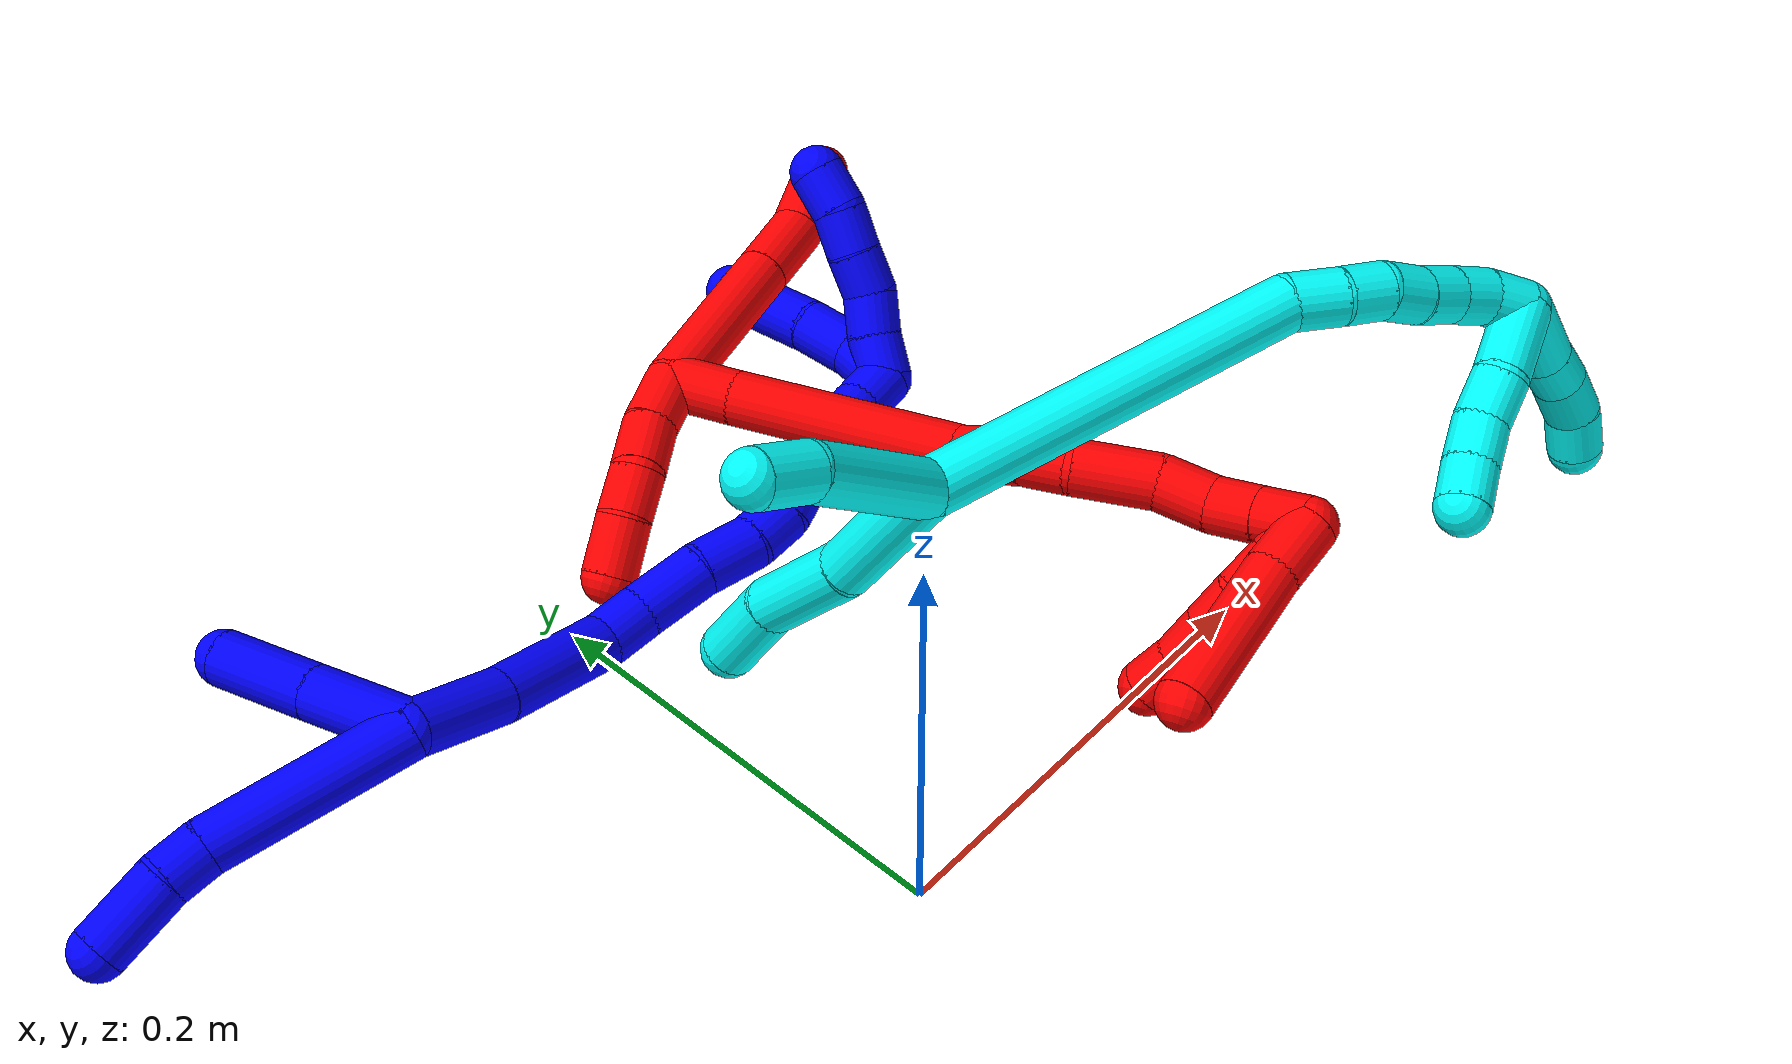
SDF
<sdf version="1.7">
 <world name="default">
  <plugin name="TubeGeneratorPlugin" filename="libtube_generator_plugin.so"/>
  <model name="photoneo_s_sensor">
   <static>1</static>
   <pose>0 0 2 1.57079 1.57079 3.14159</pose>
   <link name="link">
    <inertial><mass>0.1</mass></inertial>
    <sensor name="sensor" type="depth">
     <update_rate>30</update_rate>
     <camera>
      <horizontal_fov>1.22</horizontal_fov>
      <image><width>1920</width><height>1200</height><format>B8G8R8</format></image>
      <clip><near>0.1</near><far>4</far></clip>
      <depth_camera><output>points</output></depth_camera>
     </camera>
     <plugin name="camera_plugin" filename="libgazebo_ros_depth_camera.so">
      <baseline>0.2</baseline>
      <alwaysOn>1</alwaysOn>
      <updateRate>0.0</updateRate>
      <cameraName>camera_ir</cameraName>
      <imageTopicName>/camera/color/image_raw</imageTopicName>
      <cameraInfoTopicName>/camera/color/camera_info</cameraInfoTopicName>
      <depthImageTopicName>/camera/depth/image_raw</depthImageTopicName>
      <depthImageCameraInfoTopicName>/camera/depth/camera_info</depthImageCameraInfoTopicName>
      <pointCloudTopicName>/camera/depth/points</pointCloudTopicName>
      <frameName>fr_optical</frameName>
      <pointCloudCutoff>0.1</pointCloudCutoff>
      <pointCloudCutoffMax>2.0</pointCloudCutoffMax>
      <distortionK1>0</distortionK1>
      <distortionK2>0</distortionK2>
      <distortionK3>0</distortionK3>
      <distortionT1>0</distortionT1>
      <distortionT2>0</distortionT2>
      <CxPrime>0</CxPrime>
      <Cx>0</Cx>
      <Cy>0</Cy>
      <focalLength>0</focalLength>
      <hackBaseline>0</hackBaseline>
     </plugin>
    </sensor>
   </link>
  </model>
  <gravity>0 0 -9.8</gravity>
  <magnetic_field>6e-06 2.3e-05 -4.2e-05</magnetic_field>
  <atmosphere type="adiabatic"/>
  <physics name="default_physics" default="0" type="ode">
   <max_step_size>0.003</max_step_size>
   <real_time_factor>1</real_time_factor>
   <real_time_update_rate>1000</real_time_update_rate>
   <max_contacts>10000</max_contacts>
   <ode>
    <solver>
     <type>quick</type>
     <iters>100</iters>
     <sor>1.3</sor>
     <use_dynamic_moi_rescaling>0</use_dynamic_moi_rescaling>
    </solver>
    <constraints>
     <contact_max_correcting_vel>0</contact_max_correcting_vel>
     <contact_surface_layer>0.001</contact_surface_layer>
     <cfm>0</cfm>
     <erp>0.2</erp>
    </constraints>
   </ode>
  </physics>
  <scene><ambient>0.4 0.4 0.4 1</ambient><background>0.7 0.7 0.7 1</background><shadows>0</shadows></scene>
  <audio><device>default</device></audio>
  <spherical_coordinates>
   <surface_model>EARTH_WGS84</surface_model>
   <latitude_deg>0</latitude_deg>
   <longitude_deg>0</longitude_deg>
   <elevation>0</elevation>
   <heading_deg>0</heading_deg>
  </spherical_coordinates>
  <model name="bin">
   <static>1</static>
   <link name="bottom">
    <collision name="collision-bottom">
     <pose>0 0 -0.01 0 -0 0</pose>
     <geometry><box><size>0.8 0.6 0.02</size></box></geometry>
     <surface>
      <friction><ode><mu>100</mu><mu2>100</mu2></ode></friction>
      <contact><collide_bitmask>65535</collide_bitmask></contact>
     </surface>
    </collision>
   </link>
   <link name="west_wall">
    <collision name="collision-west_wall">
     <pose>-0.41 0 0.1 0 -0 0</pose>
     <geometry><box><size>0.02 0.6 0.2</size></box></geometry>
     <surface>
      <friction><ode><mu>100</mu><mu2>100</mu2></ode></friction>
      <contact><collide_bitmask>65535</collide_bitmask></contact>
     </surface>
    </collision>
   </link>
   <link name="east_wall">
    <collision name="collision-east_wall">
     <pose>0.41 0 0.1 0 -0 0</pose>
     <geometry><box><size>0.02 0.6 0.2</size></box></geometry>
     <surface>
      <friction><ode><mu>100</mu><mu2>100</mu2></ode></friction>
      <contact><collide_bitmask>65535</collide_bitmask></contact>
     </surface>
    </collision>
   </link>
   <link name="south_wall">
    <collision name="collision-south_wall">
     <pose>0 -0.31 0.1 0 -0 0</pose>
     <geometry><box><size>0.8 0.02 0.2</size></box></geometry>
     <surface>
      <friction><ode><mu>100</mu><mu2>100</mu2></ode></friction>
      <contact><collide_bitmask>65535</collide_bitmask></contact>
     </surface>
    </collision>
   </link>
   <link name="north_wall">
    <collision name="collision-north_wall">
     <pose>0 0.31 0.1 0 -0 0</pose>
     <geometry><box><size>0.8 0.02 0.2</size></box></geometry>
     <surface>
      <friction><ode><mu>100</mu><mu2>100</mu2></ode></friction>
      <contact><collide_bitmask>65535</collide_bitmask></contact>
     </surface>
    </collision>
   </link>
  </model>
  <model name="1">
   <static>0</static>
   <link name="1">
    <collision name="collision-cylinder-e_1_2_8">
     <pose>-0.037818 -0.020803 -0.017331 2.2654 -0.949428 -1.66327</pose>
     <geometry><cylinder><radius>0.0125</radius><length>0.093023</length></cylinder></geometry>
     <surface>
      <friction><ode><mu>1.16</mu><mu2>1.16</mu2><slip1>0</slip1><slip2>0</slip2></ode></friction>
      <contact><ode><kp>1e+06</kp><kd>1</kd><max_vel>0</max_vel><min_depth>0.001</min_depth></ode></contact>
     </surface>
    </collision>
    <visual name="visual-cylinder-e_1_2_8">
     <pose>-0.037818 -0.020803 -0.017331 2.2654 -0.949428 -1.66327</pose>
     <geometry><cylinder><radius>0.0125</radius><length>0.093023</length></cylinder></geometry>
     <material><ambient>0 0 1 1</ambient></material>
    </visual>
    <collision name="collision-cylinder-e_2_8_9">
     <pose>-0.084706 -0.044433 -0.037958 2.43257 -1.12434 -2.07914</pose>
     <geometry><cylinder><radius>0.0125</radius><length>0.020113</length></cylinder></geometry>
     <surface>
      <friction><ode><mu>1.16</mu><mu2>1.16</mu2><slip1>0</slip1><slip2>0</slip2></ode></friction>
      <contact><ode><kp>1e+06</kp><kd>1</kd><max_vel>0</max_vel><min_depth>0.001</min_depth></ode></contact>
     </surface>
    </collision>
    <visual name="visual-cylinder-e_2_8_9">
     <pose>-0.084706 -0.044433 -0.037958 2.43257 -1.12434 -2.07914</pose>
     <geometry><cylinder><radius>0.0125</radius><length>0.020113</length></cylinder></geometry>
     <material><ambient>0 0 1 1</ambient></material>
    </visual>
    <collision name="collision-cylinder-e_3_9_6">
     <pose>-0.111309 -0.052255 -0.043977 2.07005 -1.25703 -1.77177</pose>
     <geometry><cylinder><radius>0.0125</radius><length>0.036864</length></cylinder></geometry>
     <surface>
      <friction><ode><mu>1.16</mu><mu2>1.16</mu2><slip1>0</slip1><slip2>0</slip2></ode></friction>
      <contact><ode><kp>1e+06</kp><kd>1</kd><max_vel>0</max_vel><min_depth>0.001</min_depth></ode></contact>
     </surface>
    </collision>
    <visual name="visual-cylinder-e_3_9_6">
     <pose>-0.111309 -0.052255 -0.043977 2.07005 -1.25703 -1.77177</pose>
     <geometry><cylinder><radius>0.0125</radius><length>0.036864</length></cylinder></geometry>
     <material><ambient>0 0 1 1</ambient></material>
    </visual>
    <collision name="collision-cylinder-e_1_2_10">
     <pose>0.000825 -0.024478 -0.005844 1.80515 0.032773 0.041516</pose>
     <geometry><cylinder><radius>0.0125</radius><length>0.050359</length></cylinder></geometry>
     <surface>
      <friction><ode><mu>1.16</mu><mu2>1.16</mu2><slip1>0</slip1><slip2>0</slip2></ode></friction>
      <contact><ode><kp>1e+06</kp><kd>1</kd><max_vel>0</max_vel><min_depth>0.001</min_depth></ode></contact>
     </surface>
    </collision>
    <visual name="visual-cylinder-e_1_2_10">
     <pose>0.000825 -0.024478 -0.005844 1.80515 0.032773 0.041516</pose>
     <geometry><cylinder><radius>0.0125</radius><length>0.050359</length></cylinder></geometry>
     <material><ambient>0 0 1 1</ambient></material>
    </visual>
    <collision name="collision-cylinder-e_2_10_5">
     <pose>0.002603 -0.073056 -0.017547 1.80929 0.038411 0.048865</pose>
     <geometry><cylinder><radius>0.0125</radius><length>0.049641</length></cylinder></geometry>
     <surface>
      <friction><ode><mu>1.16</mu><mu2>1.16</mu2><slip1>0</slip1><slip2>0</slip2></ode></friction>
      <contact><ode><kp>1e+06</kp><kd>1</kd><max_vel>0</max_vel><min_depth>0.001</min_depth></ode></contact>
     </surface>
    </collision>
    <visual name="visual-cylinder-e_2_10_5">
     <pose>0.002603 -0.073056 -0.017547 1.80929 0.038411 0.048865</pose>
     <geometry><cylinder><radius>0.0125</radius><length>0.049641</length></cylinder></geometry>
     <material><ambient>0 0 1 1</ambient></material>
    </visual>
    <collision name="collision-cylinder-e_1_2_11">
     <pose>0.015554 0.001136 0.01692 -0.067053 0.742231 -0.026102</pose>
     <geometry><cylinder><radius>0.0125</radius><length>0.046022</length></cylinder></geometry>
     <surface>
      <friction><ode><mu>1.16</mu><mu2>1.16</mu2><slip1>0</slip1><slip2>0</slip2></ode></friction>
      <contact><ode><kp>1e+06</kp><kd>1</kd><max_vel>0</max_vel><min_depth>0.001</min_depth></ode></contact>
     </surface>
    </collision>
    <visual name="visual-cylinder-e_1_2_11">
     <pose>0.015554 0.001136 0.01692 -0.067053 0.742231 -0.026102</pose>
     <geometry><cylinder><radius>0.0125</radius><length>0.046022</length></cylinder></geometry>
     <material><ambient>0 0 1 1</ambient></material>
    </visual>
    <collision name="collision-cylinder-e_2_11_12">
     <pose>0.053388 0.002446 0.054031 -0.008589 0.834542 -0.003807</pose>
     <geometry><cylinder><radius>0.0125</radius><length>0.060138</length></cylinder></geometry>
     <surface>
      <friction><ode><mu>1.16</mu><mu2>1.16</mu2><slip1>0</slip1><slip2>0</slip2></ode></friction>
      <contact><ode><kp>1e+06</kp><kd>1</kd><max_vel>0</max_vel><min_depth>0.001</min_depth></ode></contact>
     </surface>
    </collision>
    <visual name="visual-cylinder-e_2_11_12">
     <pose>0.053388 0.002446 0.054031 -0.008589 0.834542 -0.003807</pose>
     <geometry><cylinder><radius>0.0125</radius><length>0.060138</length></cylinder></geometry>
     <material><ambient>0 0 1 1</ambient></material>
    </visual>
    <collision name="collision-cylinder-e_3_12_13">
     <pose>0.085452 0.004614 0.079105 -0.387781 1.07633 -0.233362</pose>
     <geometry><cylinder><radius>0.0125</radius><length>0.022228</length></cylinder></geometry>
     <surface>
      <friction><ode><mu>1.16</mu><mu2>1.16</mu2><slip1>0</slip1><slip2>0</slip2></ode></friction>
      <contact><ode><kp>1e+06</kp><kd>1</kd><max_vel>0</max_vel><min_depth>0.001</min_depth></ode></contact>
     </surface>
    </collision>
    <visual name="visual-cylinder-e_3_12_13">
     <pose>0.085452 0.004614 0.079105 -0.387781 1.07633 -0.233362</pose>
     <geometry><cylinder><radius>0.0125</radius><length>0.022228</length></cylinder></geometry>
     <material><ambient>0 0 1 1</ambient></material>
    </visual>
    <collision name="collision-cylinder-e_4_13_14">
     <pose>0.109452 0.011517 0.09015 -0.672629 1.0648 -0.406245</pose>
     <geometry><cylinder><radius>0.0125</radius><length>0.032509</length></cylinder></geometry>
     <surface>
      <friction><ode><mu>1.16</mu><mu2>1.16</mu2><slip1>0</slip1><slip2>0</slip2></ode></friction>
      <contact><ode><kp>1e+06</kp><kd>1</kd><max_vel>0</max_vel><min_depth>0.001</min_depth></ode></contact>
     </surface>
    </collision>
    <visual name="visual-cylinder-e_4_13_14">
     <pose>0.109452 0.011517 0.09015 -0.672629 1.0648 -0.406245</pose>
     <geometry><cylinder><radius>0.0125</radius><length>0.032509</length></cylinder></geometry>
     <material><ambient>0 0 1 1</ambient></material>
    </visual>
    <collision name="collision-cylinder-e_5_14_15">
     <pose>0.134884 0.020414 0.103636 -0.498705 0.931374 -0.254568</pose>
     <geometry><cylinder><radius>0.0125</radius><length>0.027951</length></cylinder></geometry>
     <surface>
      <friction><ode><mu>1.16</mu><mu2>1.16</mu2><slip1>0</slip1><slip2>0</slip2></ode></friction>
      <contact><ode><kp>1e+06</kp><kd>1</kd><max_vel>0</max_vel><min_depth>0.001</min_depth></ode></contact>
     </surface>
    </collision>
    <visual name="visual-cylinder-e_5_14_15">
     <pose>0.134884 0.020414 0.103636 -0.498705 0.931374 -0.254568</pose>
     <geometry><cylinder><radius>0.0125</radius><length>0.027951</length></cylinder></geometry>
     <material><ambient>0 0 1 1</ambient></material>
    </visual>
    <collision name="collision-cylinder-e_6_15_16">
     <pose>0.15535 0.025595 0.115316 -0.267162 1.11659 -0.16747</pose>
     <geometry><cylinder><radius>0.0125</radius><length>0.020592</length></cylinder></geometry>
     <surface>
      <friction><ode><mu>1.16</mu><mu2>1.16</mu2><slip1>0</slip1><slip2>0</slip2></ode></friction>
      <contact><ode><kp>1e+06</kp><kd>1</kd><max_vel>0</max_vel><min_depth>0.001</min_depth></ode></contact>
     </surface>
    </collision>
    <visual name="visual-cylinder-e_6_15_16">
     <pose>0.15535 0.025595 0.115316 -0.267162 1.11659 -0.16747</pose>
     <geometry><cylinder><radius>0.0125</radius><length>0.020592</length></cylinder></geometry>
     <material><ambient>0 0 1 1</ambient></material>
    </visual>
    <collision name="collision-cylinder-e_7_16_17">
     <pose>0.178566 0.026159 0.121743 0.294725 1.41712 0.253071</pose>
     <geometry><cylinder><radius>0.0125</radius><length>0.02826</length></cylinder></geometry>
     <surface>
      <friction><ode><mu>1.16</mu><mu2>1.16</mu2><slip1>0</slip1><slip2>0</slip2></ode></friction>
      <contact><ode><kp>1e+06</kp><kd>1</kd><max_vel>0</max_vel><min_depth>0.001</min_depth></ode></contact>
     </surface>
    </collision>
    <visual name="visual-cylinder-e_7_16_17">
     <pose>0.178566 0.026159 0.121743 0.294725 1.41712 0.253071</pose>
     <geometry><cylinder><radius>0.0125</radius><length>0.02826</length></cylinder></geometry>
     <material><ambient>0 0 1 1</ambient></material>
    </visual>
    <collision name="collision-cylinder-e_8_17_18">
     <pose>0.202384 0.02537 0.127016 0.050041 1.25615 0.036342</pose>
     <geometry><cylinder><radius>0.0125</radius><length>0.020727</length></cylinder></geometry>
     <surface>
      <friction><ode><mu>1.16</mu><mu2>1.16</mu2><slip1>0</slip1><slip2>0</slip2></ode></friction>
      <contact><ode><kp>1e+06</kp><kd>1</kd><max_vel>0</max_vel><min_depth>0.001</min_depth></ode></contact>
     </surface>
    </collision>
    <visual name="visual-cylinder-e_8_17_18">
     <pose>0.202384 0.02537 0.127016 0.050041 1.25615 0.036342</pose>
     <geometry><cylinder><radius>0.0125</radius><length>0.020727</length></cylinder></geometry>
     <material><ambient>0 0 1 1</ambient></material>
    </visual>
    <collision name="collision-cylinder-e_9_18_19">
     <pose>0.221321 0.024036 0.135049 0.238456 1.07008 0.14177</pose>
     <geometry><cylinder><radius>0.0125</radius><length>0.020706</length></cylinder></geometry>
     <surface>
      <friction><ode><mu>1.16</mu><mu2>1.16</mu2><slip1>0</slip1><slip2>0</slip2></ode></friction>
      <contact><ode><kp>1e+06</kp><kd>1</kd><max_vel>0</max_vel><min_depth>0.001</min_depth></ode></contact>
     </surface>
    </collision>
    <visual name="visual-cylinder-e_9_18_19">
     <pose>0.221321 0.024036 0.135049 0.238456 1.07008 0.14177</pose>
     <geometry><cylinder><radius>0.0125</radius><length>0.020706</length></cylinder></geometry>
     <material><ambient>0 0 1 1</ambient></material>
    </visual>
    <collision name="collision-cylinder-e_10_19_1">
     <pose>0.239971 0.023037 0.144037 -0.042035 1.16051 -0.027558</pose>
     <geometry><cylinder><radius>0.0125</radius><length>0.020868</length></cylinder></geometry>
     <surface>
      <friction><ode><mu>1.16</mu><mu2>1.16</mu2><slip1>0</slip1><slip2>0</slip2></ode></friction>
      <contact><ode><kp>1e+06</kp><kd>1</kd><max_vel>0</max_vel><min_depth>0.001</min_depth></ode></contact>
     </surface>
    </collision>
    <visual name="visual-cylinder-e_10_19_1">
     <pose>0.239971 0.023037 0.144037 -0.042035 1.16051 -0.027558</pose>
     <geometry><cylinder><radius>0.0125</radius><length>0.020868</length></cylinder></geometry>
     <material><ambient>0 0 1 1</ambient></material>
    </visual>
    <collision name="collision-cylinder-e_1_1_20">
     <pose>0.254432 0.0128 0.146353 1.74587 0.433426 0.513478</pose>
     <geometry><cylinder><radius>0.0125</radius><length>0.023301</length></cylinder></geometry>
     <surface>
      <friction><ode><mu>1.16</mu><mu2>1.16</mu2><slip1>0</slip1><slip2>0</slip2></ode></friction>
      <contact><ode><kp>1e+06</kp><kd>1</kd><max_vel>0</max_vel><min_depth>0.001</min_depth></ode></contact>
     </surface>
    </collision>
    <visual name="visual-cylinder-e_1_1_20">
     <pose>0.254432 0.0128 0.146353 1.74587 0.433426 0.513478</pose>
     <geometry><cylinder><radius>0.0125</radius><length>0.023301</length></cylinder></geometry>
     <material><ambient>0 0 1 1</ambient></material>
    </visual>
    <collision name="collision-cylinder-e_2_20_21">
     <pose>0.26252 -0.010134 0.140672 1.86831 0.239202 0.322269</pose>
     <geometry><cylinder><radius>0.0125</radius><length>0.026965</length></cylinder></geometry>
     <surface>
      <friction><ode><mu>1.16</mu><mu2>1.16</mu2><slip1>0</slip1><slip2>0</slip2></ode></friction>
      <contact><ode><kp>1e+06</kp><kd>1</kd><max_vel>0</max_vel><min_depth>0.001</min_depth></ode></contact>
     </surface>
    </collision>
    <visual name="visual-cylinder-e_2_20_21">
     <pose>0.26252 -0.010134 0.140672 1.86831 0.239202 0.322269</pose>
     <geometry><cylinder><radius>0.0125</radius><length>0.026965</length></cylinder></geometry>
     <material><ambient>0 0 1 1</ambient></material>
    </visual>
    <collision name="collision-cylinder-e_3_21_4">
     <pose>0.270521 -0.046717 0.132783 1.73751 0.194519 0.229701</pose>
     <geometry><cylinder><radius>0.0125</radius><length>0.049734</length></cylinder></geometry>
     <surface>
      <friction><ode><mu>1.16</mu><mu2>1.16</mu2><slip1>0</slip1><slip2>0</slip2></ode></friction>
      <contact><ode><kp>1e+06</kp><kd>1</kd><max_vel>0</max_vel><min_depth>0.001</min_depth></ode></contact>
     </surface>
    </collision>
    <visual name="visual-cylinder-e_3_21_4">
     <pose>0.270521 -0.046717 0.132783 1.73751 0.194519 0.229701</pose>
     <geometry><cylinder><radius>0.0125</radius><length>0.049734</length></cylinder></geometry>
     <material><ambient>0 0 1 1</ambient></material>
    </visual>
    <collision name="collision-cylinder-e_1_1_22">
     <pose>0.257352 0.019682 0.143047 2.5405 0.896708 1.99685</pose>
     <geometry><cylinder><radius>0.0125</radius><length>0.02</length></cylinder></geometry>
     <surface>
      <friction><ode><mu>1.16</mu><mu2>1.16</mu2><slip1>0</slip1><slip2>0</slip2></ode></friction>
      <contact><ode><kp>1e+06</kp><kd>1</kd><max_vel>0</max_vel><min_depth>0.001</min_depth></ode></contact>
     </surface>
    </collision>
    <visual name="visual-cylinder-e_1_1_22">
     <pose>0.257352 0.019682 0.143047 2.5405 0.896708 1.99685</pose>
     <geometry><cylinder><radius>0.0125</radius><length>0.02</length></cylinder></geometry>
     <material><ambient>0 0 1 1</ambient></material>
    </visual>
    <collision name="collision-cylinder-e_2_22_23">
     <pose>0.273379 0.014421 0.132466 2.83314 0.96396 2.56387</pose>
     <geometry><cylinder><radius>0.0125</radius><length>0.02</length></cylinder></geometry>
     <surface>
      <friction><ode><mu>1.16</mu><mu2>1.16</mu2><slip1>0</slip1><slip2>0</slip2></ode></friction>
      <contact><ode><kp>1e+06</kp><kd>1</kd><max_vel>0</max_vel><min_depth>0.001</min_depth></ode></contact>
     </surface>
    </collision>
    <visual name="visual-cylinder-e_2_22_23">
     <pose>0.273379 0.014421 0.132466 2.83314 0.96396 2.56387</pose>
     <geometry><cylinder><radius>0.0125</radius><length>0.02</length></cylinder></geometry>
     <material><ambient>0 0 1 1</ambient></material>
    </visual>
    <collision name="collision-cylinder-e_3_23_24">
     <pose>0.287532 0.010101 0.119413 2.81416 0.63573 2.21097</pose>
     <geometry><cylinder><radius>0.0125</radius><length>0.02</length></cylinder></geometry>
     <surface>
      <friction><ode><mu>1.16</mu><mu2>1.16</mu2><slip1>0</slip1><slip2>0</slip2></ode></friction>
      <contact><ode><kp>1e+06</kp><kd>1</kd><max_vel>0</max_vel><min_depth>0.001</min_depth></ode></contact>
     </surface>
    </collision>
    <visual name="visual-cylinder-e_3_23_24">
     <pose>0.287532 0.010101 0.119413 2.81416 0.63573 2.21097</pose>
     <geometry><cylinder><radius>0.0125</radius><length>0.02</length></cylinder></geometry>
     <material><ambient>0 0 1 1</ambient></material>
    </visual>
    <collision name="collision-cylinder-e_4_24_25">
     <pose>0.30011 0.00459 0.104913 2.73982 0.726202 2.15761</pose>
     <geometry><cylinder><radius>0.0125</radius><length>0.02</length></cylinder></geometry>
     <surface>
      <friction><ode><mu>1.16</mu><mu2>1.16</mu2><slip1>0</slip1><slip2>0</slip2></ode></friction>
      <contact><ode><kp>1e+06</kp><kd>1</kd><max_vel>0</max_vel><min_depth>0.001</min_depth></ode></contact>
     </surface>
    </collision>
    <visual name="visual-cylinder-e_4_24_25">
     <pose>0.30011 0.00459 0.104913 2.73982 0.726202 2.15761</pose>
     <geometry><cylinder><radius>0.0125</radius><length>0.02</length></cylinder></geometry>
     <material><ambient>0 0 1 1</ambient></material>
    </visual>
    <collision name="collision-cylinder-e_5_25_3">
     <pose>0.312497 -0.003536 0.091713 2.45283 0.612216 1.44459</pose>
     <geometry><cylinder><radius>0.0125</radius><length>0.02</length></cylinder></geometry>
     <surface>
      <friction><ode><mu>1.16</mu><mu2>1.16</mu2><slip1>0</slip1><slip2>0</slip2></ode></friction>
      <contact><ode><kp>1e+06</kp><kd>1</kd><max_vel>0</max_vel><min_depth>0.001</min_depth></ode></contact>
     </surface>
    </collision>
    <visual name="visual-cylinder-e_5_25_3">
     <pose>0.312497 -0.003536 0.091713 2.45283 0.612216 1.44459</pose>
     <geometry><cylinder><radius>0.0125</radius><length>0.02</length></cylinder></geometry>
     <material><ambient>0 0 1 1</ambient></material>
    </visual>
    <collision name="collision-sphere-3">
     <pose>0.318244 -0.008737 0.085395 0 -0 0</pose>
     <geometry><sphere><radius>0.0125</radius></sphere></geometry>
     <surface>
      <friction><ode><mu>1.16</mu><mu2>1.16</mu2><slip1>0</slip1><slip2>0</slip2></ode></friction>
      <contact><ode><kp>1e+06</kp><kd>1</kd><max_vel>0</max_vel><min_depth>0.001</min_depth></ode></contact>
     </surface>
    </collision>
    <visual name="visual-sphere-3">
     <pose>0.318244 -0.008737 0.085395 0 -0 0</pose>
     <geometry><sphere><radius>0.0125</radius></sphere></geometry>
     <material><ambient>0 0 1 1</ambient></material>
    </visual>
    <collision name="collision-sphere-25">
     <pose>0.30675 0.001666 0.098031 0 -0 0</pose>
     <geometry><sphere><radius>0.0125</radius></sphere></geometry>
     <surface>
      <friction><ode><mu>1.16</mu><mu2>1.16</mu2><slip1>0</slip1><slip2>0</slip2></ode></friction>
      <contact><ode><kp>1e+06</kp><kd>1</kd><max_vel>0</max_vel><min_depth>0.001</min_depth></ode></contact>
     </surface>
    </collision>
    <visual name="visual-sphere-25">
     <pose>0.30675 0.001666 0.098031 0 -0 0</pose>
     <geometry><sphere><radius>0.0125</radius></sphere></geometry>
     <material><ambient>0 0 1 1</ambient></material>
    </visual>
    <collision name="collision-sphere-24">
     <pose>0.293469 0.007514 0.111794 0 -0 0</pose>
     <geometry><sphere><radius>0.0125</radius></sphere></geometry>
     <surface>
      <friction><ode><mu>1.16</mu><mu2>1.16</mu2><slip1>0</slip1><slip2>0</slip2></ode></friction>
      <contact><ode><kp>1e+06</kp><kd>1</kd><max_vel>0</max_vel><min_depth>0.001</min_depth></ode></contact>
     </surface>
    </collision>
    <visual name="visual-sphere-24">
     <pose>0.293469 0.007514 0.111794 0 -0 0</pose>
     <geometry><sphere><radius>0.0125</radius></sphere></geometry>
     <material><ambient>0 0 1 1</ambient></material>
    </visual>
    <collision name="collision-sphere-23">
     <pose>0.281594 0.012689 0.127032 0 -0 0</pose>
     <geometry><sphere><radius>0.0125</radius></sphere></geometry>
     <surface>
      <friction><ode><mu>1.16</mu><mu2>1.16</mu2><slip1>0</slip1><slip2>0</slip2></ode></friction>
      <contact><ode><kp>1e+06</kp><kd>1</kd><max_vel>0</max_vel><min_depth>0.001</min_depth></ode></contact>
     </surface>
    </collision>
    <visual name="visual-sphere-23">
     <pose>0.281594 0.012689 0.127032 0 -0 0</pose>
     <geometry><sphere><radius>0.0125</radius></sphere></geometry>
     <material><ambient>0 0 1 1</ambient></material>
    </visual>
    <collision name="collision-sphere-22">
     <pose>0.265165 0.016152 0.137899 0 -0 0</pose>
     <geometry><sphere><radius>0.0125</radius></sphere></geometry>
     <surface>
      <friction><ode><mu>1.16</mu><mu2>1.16</mu2><slip1>0</slip1><slip2>0</slip2></ode></friction>
      <contact><ode><kp>1e+06</kp><kd>1</kd><max_vel>0</max_vel><min_depth>0.001</min_depth></ode></contact>
     </surface>
    </collision>
    <visual name="visual-sphere-22">
     <pose>0.265165 0.016152 0.137899 0 -0 0</pose>
     <geometry><sphere><radius>0.0125</radius></sphere></geometry>
     <material><ambient>0 0 1 1</ambient></material>
    </visual>
    <collision name="collision-sphere-4">
     <pose>0.275327 -0.070777 0.128734 0 -0 0</pose>
     <geometry><sphere><radius>0.0125</radius></sphere></geometry>
     <surface>
      <friction><ode><mu>1.16</mu><mu2>1.16</mu2><slip1>0</slip1><slip2>0</slip2></ode></friction>
      <contact><ode><kp>1e+06</kp><kd>1</kd><max_vel>0</max_vel><min_depth>0.001</min_depth></ode></contact>
     </surface>
    </collision>
    <visual name="visual-sphere-4">
     <pose>0.275327 -0.070777 0.128734 0 -0 0</pose>
     <geometry><sphere><radius>0.0125</radius></sphere></geometry>
     <material><ambient>0 0 1 1</ambient></material>
    </visual>
    <collision name="collision-sphere-21">
     <pose>0.265714 -0.022657 0.136832 0 -0 0</pose>
     <geometry><sphere><radius>0.0125</radius></sphere></geometry>
     <surface>
      <friction><ode><mu>1.16</mu><mu2>1.16</mu2><slip1>0</slip1><slip2>0</slip2></ode></friction>
      <contact><ode><kp>1e+06</kp><kd>1</kd><max_vel>0</max_vel><min_depth>0.001</min_depth></ode></contact>
     </surface>
    </collision>
    <visual name="visual-sphere-21">
     <pose>0.265714 -0.022657 0.136832 0 -0 0</pose>
     <geometry><sphere><radius>0.0125</radius></sphere></geometry>
     <material><ambient>0 0 1 1</ambient></material>
    </visual>
    <collision name="collision-sphere-20">
     <pose>0.259325 0.002389 0.144512 0 -0 0</pose>
     <geometry><sphere><radius>0.0125</radius></sphere></geometry>
     <surface>
      <friction><ode><mu>1.16</mu><mu2>1.16</mu2><slip1>0</slip1><slip2>0</slip2></ode></friction>
      <contact><ode><kp>1e+06</kp><kd>1</kd><max_vel>0</max_vel><min_depth>0.001</min_depth></ode></contact>
     </surface>
    </collision>
    <visual name="visual-sphere-20">
     <pose>0.259325 0.002389 0.144512 0 -0 0</pose>
     <geometry><sphere><radius>0.0125</radius></sphere></geometry>
     <material><ambient>0 0 1 1</ambient></material>
    </visual>
    <collision name="collision-sphere-5">
     <pose>0.003556 -0.097156 -0.023406 0 -0 0</pose>
     <geometry><sphere><radius>0.0125</radius></sphere></geometry>
     <surface>
      <friction><ode><mu>1.16</mu><mu2>1.16</mu2><slip1>0</slip1><slip2>0</slip2></ode></friction>
      <contact><ode><kp>1e+06</kp><kd>1</kd><max_vel>0</max_vel><min_depth>0.001</min_depth></ode></contact>
     </surface>
    </collision>
    <visual name="visual-sphere-5">
     <pose>0.003556 -0.097156 -0.023406 0 -0 0</pose>
     <geometry><sphere><radius>0.0125</radius></sphere></geometry>
     <material><ambient>0 0 1 1</ambient></material>
    </visual>
    <collision name="collision-sphere-10">
     <pose>0.00165 -0.048956 -0.011688 0 -0 0</pose>
     <geometry><sphere><radius>0.0125</radius></sphere></geometry>
     <surface>
      <friction><ode><mu>1.16</mu><mu2>1.16</mu2><slip1>0</slip1><slip2>0</slip2></ode></friction>
      <contact><ode><kp>1e+06</kp><kd>1</kd><max_vel>0</max_vel><min_depth>0.001</min_depth></ode></contact>
     </surface>
    </collision>
    <visual name="visual-sphere-10">
     <pose>0.00165 -0.048956 -0.011688 0 -0 0</pose>
     <geometry><sphere><radius>0.0125</radius></sphere></geometry>
     <material><ambient>0 0 1 1</ambient></material>
    </visual>
    <collision name="collision-sphere-6">
     <pose>-0.128841 -0.057249 -0.046701 0 -0 0</pose>
     <geometry><sphere><radius>0.0125</radius></sphere></geometry>
     <surface>
      <friction><ode><mu>1.16</mu><mu2>1.16</mu2><slip1>0</slip1><slip2>0</slip2></ode></friction>
      <contact><ode><kp>1e+06</kp><kd>1</kd><max_vel>0</max_vel><min_depth>0.001</min_depth></ode></contact>
     </surface>
    </collision>
    <visual name="visual-sphere-6">
     <pose>-0.128841 -0.057249 -0.046701 0 -0 0</pose>
     <geometry><sphere><radius>0.0125</radius></sphere></geometry>
     <material><ambient>0 0 1 1</ambient></material>
    </visual>
    <collision name="collision-sphere-9">
     <pose>-0.093777 -0.04726 -0.041254 0 -0 0</pose>
     <geometry><sphere><radius>0.0125</radius></sphere></geometry>
     <surface>
      <friction><ode><mu>1.16</mu><mu2>1.16</mu2><slip1>0</slip1><slip2>0</slip2></ode></friction>
      <contact><ode><kp>1e+06</kp><kd>1</kd><max_vel>0</max_vel><min_depth>0.001</min_depth></ode></contact>
     </surface>
    </collision>
    <visual name="visual-sphere-9">
     <pose>-0.093777 -0.04726 -0.041254 0 -0 0</pose>
     <geometry><sphere><radius>0.0125</radius></sphere></geometry>
     <material><ambient>0 0 1 1</ambient></material>
    </visual>
    <collision name="collision-sphere-2">
     <geometry><sphere><radius>0.0125</radius></sphere></geometry>
     <surface>
      <friction><ode><mu>1.16</mu><mu2>1.16</mu2><slip1>0</slip1><slip2>0</slip2></ode></friction>
      <contact><ode><kp>1e+06</kp><kd>1</kd><max_vel>0</max_vel><min_depth>0.001</min_depth></ode></contact>
     </surface>
    </collision>
    <visual name="visual-sphere-2">
     <geometry><sphere><radius>0.0125</radius></sphere></geometry>
     <material><ambient>0 0 1 1</ambient></material>
    </visual>
    <collision name="collision-sphere-19">
     <pose>0.230403 0.022862 0.139879 0 -0 0</pose>
     <geometry><sphere><radius>0.0125</radius></sphere></geometry>
     <surface>
      <friction><ode><mu>1.16</mu><mu2>1.16</mu2><slip1>0</slip1><slip2>0</slip2></ode></friction>
      <contact><ode><kp>1e+06</kp><kd>1</kd><max_vel>0</max_vel><min_depth>0.001</min_depth></ode></contact>
     </surface>
    </collision>
    <visual name="visual-sphere-19">
     <pose>0.230403 0.022862 0.139879 0 -0 0</pose>
     <geometry><sphere><radius>0.0125</radius></sphere></geometry>
     <material><ambient>0 0 1 1</ambient></material>
    </visual>
    <collision name="collision-sphere-8">
     <pose>-0.075635 -0.041606 -0.034662 0 -0 0</pose>
     <geometry><sphere><radius>0.0125</radius></sphere></geometry>
     <surface>
      <friction><ode><mu>1.16</mu><mu2>1.16</mu2><slip1>0</slip1><slip2>0</slip2></ode></friction>
      <contact><ode><kp>1e+06</kp><kd>1</kd><max_vel>0</max_vel><min_depth>0.001</min_depth></ode></contact>
     </surface>
    </collision>
    <visual name="visual-sphere-8">
     <pose>-0.075635 -0.041606 -0.034662 0 -0 0</pose>
     <geometry><sphere><radius>0.0125</radius></sphere></geometry>
     <material><ambient>0 0 1 1</ambient></material>
    </visual>
    <collision name="collision-sphere-11">
     <pose>0.031108 0.002272 0.03384 0 -0 0</pose>
     <geometry><sphere><radius>0.0125</radius></sphere></geometry>
     <surface>
      <friction><ode><mu>1.16</mu><mu2>1.16</mu2><slip1>0</slip1><slip2>0</slip2></ode></friction>
      <contact><ode><kp>1e+06</kp><kd>1</kd><max_vel>0</max_vel><min_depth>0.001</min_depth></ode></contact>
     </surface>
    </collision>
    <visual name="visual-sphere-11">
     <pose>0.031108 0.002272 0.03384 0 -0 0</pose>
     <geometry><sphere><radius>0.0125</radius></sphere></geometry>
     <material><ambient>0 0 1 1</ambient></material>
    </visual>
    <collision name="collision-sphere-12">
     <pose>0.075669 0.002619 0.074222 0 -0 0</pose>
     <geometry><sphere><radius>0.0125</radius></sphere></geometry>
     <surface>
      <friction><ode><mu>1.16</mu><mu2>1.16</mu2><slip1>0</slip1><slip2>0</slip2></ode></friction>
      <contact><ode><kp>1e+06</kp><kd>1</kd><max_vel>0</max_vel><min_depth>0.001</min_depth></ode></contact>
     </surface>
    </collision>
    <visual name="visual-sphere-12">
     <pose>0.075669 0.002619 0.074222 0 -0 0</pose>
     <geometry><sphere><radius>0.0125</radius></sphere></geometry>
     <material><ambient>0 0 1 1</ambient></material>
    </visual>
    <collision name="collision-sphere-13">
     <pose>0.095235 0.006608 0.083987 0 -0 0</pose>
     <geometry><sphere><radius>0.0125</radius></sphere></geometry>
     <surface>
      <friction><ode><mu>1.16</mu><mu2>1.16</mu2><slip1>0</slip1><slip2>0</slip2></ode></friction>
      <contact><ode><kp>1e+06</kp><kd>1</kd><max_vel>0</max_vel><min_depth>0.001</min_depth></ode></contact>
     </surface>
    </collision>
    <visual name="visual-sphere-13">
     <pose>0.095235 0.006608 0.083987 0 -0 0</pose>
     <geometry><sphere><radius>0.0125</radius></sphere></geometry>
     <material><ambient>0 0 1 1</ambient></material>
    </visual>
    <collision name="collision-sphere-14">
     <pose>0.12367 0.016425 0.096312 0 -0 0</pose>
     <geometry><sphere><radius>0.0125</radius></sphere></geometry>
     <surface>
      <friction><ode><mu>1.16</mu><mu2>1.16</mu2><slip1>0</slip1><slip2>0</slip2></ode></friction>
      <contact><ode><kp>1e+06</kp><kd>1</kd><max_vel>0</max_vel><min_depth>0.001</min_depth></ode></contact>
     </surface>
    </collision>
    <visual name="visual-sphere-14">
     <pose>0.12367 0.016425 0.096312 0 -0 0</pose>
     <geometry><sphere><radius>0.0125</radius></sphere></geometry>
     <material><ambient>0 0 1 1</ambient></material>
    </visual>
    <collision name="collision-sphere-15">
     <pose>0.146099 0.024402 0.110959 0 -0 0</pose>
     <geometry><sphere><radius>0.0125</radius></sphere></geometry>
     <surface>
      <friction><ode><mu>1.16</mu><mu2>1.16</mu2><slip1>0</slip1><slip2>0</slip2></ode></friction>
      <contact><ode><kp>1e+06</kp><kd>1</kd><max_vel>0</max_vel><min_depth>0.001</min_depth></ode></contact>
     </surface>
    </collision>
    <visual name="visual-sphere-15">
     <pose>0.146099 0.024402 0.110959 0 -0 0</pose>
     <geometry><sphere><radius>0.0125</radius></sphere></geometry>
     <material><ambient>0 0 1 1</ambient></material>
    </visual>
    <collision name="collision-sphere-16">
     <pose>0.164602 0.026787 0.119674 0 -0 0</pose>
     <geometry><sphere><radius>0.0125</radius></sphere></geometry>
     <surface>
      <friction><ode><mu>1.16</mu><mu2>1.16</mu2><slip1>0</slip1><slip2>0</slip2></ode></friction>
      <contact><ode><kp>1e+06</kp><kd>1</kd><max_vel>0</max_vel><min_depth>0.001</min_depth></ode></contact>
     </surface>
    </collision>
    <visual name="visual-sphere-16">
     <pose>0.164602 0.026787 0.119674 0 -0 0</pose>
     <geometry><sphere><radius>0.0125</radius></sphere></geometry>
     <material><ambient>0 0 1 1</ambient></material>
    </visual>
    <collision name="collision-sphere-17">
     <pose>0.192529 0.025531 0.123813 0 -0 0</pose>
     <geometry><sphere><radius>0.0125</radius></sphere></geometry>
     <surface>
      <friction><ode><mu>1.16</mu><mu2>1.16</mu2><slip1>0</slip1><slip2>0</slip2></ode></friction>
      <contact><ode><kp>1e+06</kp><kd>1</kd><max_vel>0</max_vel><min_depth>0.001</min_depth></ode></contact>
     </surface>
    </collision>
    <visual name="visual-sphere-17">
     <pose>0.192529 0.025531 0.123813 0 -0 0</pose>
     <geometry><sphere><radius>0.0125</radius></sphere></geometry>
     <material><ambient>0 0 1 1</ambient></material>
    </visual>
    <collision name="collision-sphere-18">
     <pose>0.212239 0.02521 0.13022 0 -0 0</pose>
     <geometry><sphere><radius>0.0125</radius></sphere></geometry>
     <surface>
      <friction><ode><mu>1.16</mu><mu2>1.16</mu2><slip1>0</slip1><slip2>0</slip2></ode></friction>
      <contact><ode><kp>1e+06</kp><kd>1</kd><max_vel>0</max_vel><min_depth>0.001</min_depth></ode></contact>
     </surface>
    </collision>
    <visual name="visual-sphere-18">
     <pose>0.212239 0.02521 0.13022 0 -0 0</pose>
     <geometry><sphere><radius>0.0125</radius></sphere></geometry>
     <material><ambient>0 0 1 1</ambient></material>
    </visual>
    <collision name="collision-sphere-1">
     <pose>0.249539 0.023212 0.148195 0 -0 0</pose>
     <geometry><sphere><radius>0.0125</radius></sphere></geometry>
     <surface>
      <friction><ode><mu>1.16</mu><mu2>1.16</mu2><slip1>0</slip1><slip2>0</slip2></ode></friction>
      <contact><ode><kp>1e+06</kp><kd>1</kd><max_vel>0</max_vel><min_depth>0.001</min_depth></ode></contact>
     </surface>
    </collision>
    <visual name="visual-sphere-1">
     <pose>0.249539 0.023212 0.148195 0 -0 0</pose>
     <geometry><sphere><radius>0.0125</radius></sphere></geometry>
     <material><ambient>0 0 1 1</ambient></material>
    </visual>
    <inertial>
     <pose>0.108146 -0.00932 0.061786 0 -0 0</pose>
     <mass>0.75</mass>
     <inertia><ixx>4.4e-05</ixx><ixy>0</ixy><ixz>0</ixz><iyy>4.5e-05</iyy><iyz>0</iyz><izz>8.9e-05</izz></inertia>
    </inertial>
   </link>
   <pose>-0.100935 0.184198 0.046282 2.71027 -0.376843 0.309939</pose>
  </model>
  <model name="2">
   <static>0</static>
   <link name="2">
    <collision name="collision-cylinder-e_1_2_8">
     <pose>0.022768 0.006553 0.033268 -0.194476 0.591324 -0.059405</pose>
     <geometry><cylinder><radius>0.0125</radius><length>0.081684</length></cylinder></geometry>
     <surface>
      <friction><ode><mu>1.16</mu><mu2>1.16</mu2><slip1>0</slip1><slip2>0</slip2></ode></friction>
      <contact><ode><kp>1e+06</kp><kd>1</kd><max_vel>0</max_vel><min_depth>0.001</min_depth></ode></contact>
     </surface>
    </collision>
    <visual name="visual-cylinder-e_1_2_8">
     <pose>0.022768 0.006553 0.033268 -0.194476 0.591324 -0.059405</pose>
     <geometry><cylinder><radius>0.0125</radius><length>0.081684</length></cylinder></geometry>
     <material><ambient>1 0 0 1</ambient></material>
    </visual>
    <collision name="collision-cylinder-e_2_8_9">
     <pose>0.055299 0.016026 0.080822 -0.201669 0.590015 -0.061471</pose>
     <geometry><cylinder><radius>0.0125</radius><length>0.035095</length></cylinder></geometry>
     <surface>
      <friction><ode><mu>1.16</mu><mu2>1.16</mu2><slip1>0</slip1><slip2>0</slip2></ode></friction>
      <contact><ode><kp>1e+06</kp><kd>1</kd><max_vel>0</max_vel><min_depth>0.001</min_depth></ode></contact>
     </surface>
    </collision>
    <visual name="visual-cylinder-e_2_8_9">
     <pose>0.055299 0.016026 0.080822 -0.201669 0.590015 -0.061471</pose>
     <geometry><cylinder><radius>0.0125</radius><length>0.035095</length></cylinder></geometry>
     <material><ambient>1 0 0 1</ambient></material>
    </visual>
    <collision name="collision-cylinder-e_3_9_6">
     <pose>0.069575 0.021511 0.110885 -0.161127 0.27519 -0.022359</pose>
     <geometry><cylinder><radius>0.0125</radius><length>0.03322</length></cylinder></geometry>
     <surface>
      <friction><ode><mu>1.16</mu><mu2>1.16</mu2><slip1>0</slip1><slip2>0</slip2></ode></friction>
      <contact><ode><kp>1e+06</kp><kd>1</kd><max_vel>0</max_vel><min_depth>0.001</min_depth></ode></contact>
     </surface>
    </collision>
    <visual name="visual-cylinder-e_3_9_6">
     <pose>0.069575 0.021511 0.110885 -0.161127 0.27519 -0.022359</pose>
     <geometry><cylinder><radius>0.0125</radius><length>0.03322</length></cylinder></geometry>
     <material><ambient>1 0 0 1</ambient></material>
    </visual>
    <collision name="collision-cylinder-e_1_2_10">
     <pose>-0.005394 -0.003063 -0.011939 2.89044 -0.412529 -2.05585</pose>
     <geometry><cylinder><radius>0.0125</radius><length>0.026908</length></cylinder></geometry>
     <surface>
      <friction><ode><mu>1.16</mu><mu2>1.16</mu2><slip1>0</slip1><slip2>0</slip2></ode></friction>
      <contact><ode><kp>1e+06</kp><kd>1</kd><max_vel>0</max_vel><min_depth>0.001</min_depth></ode></contact>
     </surface>
    </collision>
    <visual name="visual-cylinder-e_1_2_10">
     <pose>-0.005394 -0.003063 -0.011939 2.89044 -0.412529 -2.05585</pose>
     <geometry><cylinder><radius>0.0125</radius><length>0.026908</length></cylinder></geometry>
     <material><ambient>1 0 0 1</ambient></material>
    </visual>
    <collision name="collision-cylinder-e_2_10_11">
     <pose>-0.014462 -0.010707 -0.034859 2.74638 -0.299444 -1.29137</pose>
     <geometry><cylinder><radius>0.0125</radius><length>0.024904</length></cylinder></geometry>
     <surface>
      <friction><ode><mu>1.16</mu><mu2>1.16</mu2><slip1>0</slip1><slip2>0</slip2></ode></friction>
      <contact><ode><kp>1e+06</kp><kd>1</kd><max_vel>0</max_vel><min_depth>0.001</min_depth></ode></contact>
     </surface>
    </collision>
    <visual name="visual-cylinder-e_2_10_11">
     <pose>-0.014462 -0.010707 -0.034859 2.74638 -0.299444 -1.29137</pose>
     <geometry><cylinder><radius>0.0125</radius><length>0.024904</length></cylinder></geometry>
     <material><ambient>1 0 0 1</ambient></material>
    </visual>
    <collision name="collision-cylinder-e_3_11_12">
     <pose>-0.019029 -0.01667 -0.056601 3.01391 -0.082263 -1.14399</pose>
     <geometry><cylinder><radius>0.0125</radius><length>0.021774</length></cylinder></geometry>
     <surface>
      <friction><ode><mu>1.16</mu><mu2>1.16</mu2><slip1>0</slip1><slip2>0</slip2></ode></friction>
      <contact><ode><kp>1e+06</kp><kd>1</kd><max_vel>0</max_vel><min_depth>0.001</min_depth></ode></contact>
     </surface>
    </collision>
    <visual name="visual-cylinder-e_3_11_12">
     <pose>-0.019029 -0.01667 -0.056601 3.01391 -0.082263 -1.14399</pose>
     <geometry><cylinder><radius>0.0125</radius><length>0.021774</length></cylinder></geometry>
     <material><ambient>1 0 0 1</ambient></material>
    </visual>
    <collision name="collision-cylinder-e_4_12_5">
     <pose>-0.01901 -0.018345 -0.080535 3.11928 0.06928 2.51868</pose>
     <geometry><cylinder><radius>0.0125</radius><length>0.026413</length></cylinder></geometry>
     <surface>
      <friction><ode><mu>1.16</mu><mu2>1.16</mu2><slip1>0</slip1><slip2>0</slip2></ode></friction>
      <contact><ode><kp>1e+06</kp><kd>1</kd><max_vel>0</max_vel><min_depth>0.001</min_depth></ode></contact>
     </surface>
    </collision>
    <visual name="visual-cylinder-e_4_12_5">
     <pose>-0.01901 -0.018345 -0.080535 3.11928 0.06928 2.51868</pose>
     <geometry><cylinder><radius>0.0125</radius><length>0.026413</length></cylinder></geometry>
     <material><ambient>1 0 0 1</ambient></material>
    </visual>
    <collision name="collision-cylinder-e_1_2_13">
     <pose>0.006615 -0.014182 0.000151 1.56014 0.43641 0.431927</pose>
     <geometry><cylinder><radius>0.0125</radius><length>0.031299</length></cylinder></geometry>
     <surface>
      <friction><ode><mu>1.16</mu><mu2>1.16</mu2><slip1>0</slip1><slip2>0</slip2></ode></friction>
      <contact><ode><kp>1e+06</kp><kd>1</kd><max_vel>0</max_vel><min_depth>0.001</min_depth></ode></contact>
     </surface>
    </collision>
    <visual name="visual-cylinder-e_1_2_13">
     <pose>0.006615 -0.014182 0.000151 1.56014 0.43641 0.431927</pose>
     <geometry><cylinder><radius>0.0125</radius><length>0.031299</length></cylinder></geometry>
     <material><ambient>1 0 0 1</ambient></material>
    </visual>
    <collision name="collision-cylinder-e_2_13_14">
     <pose>0.031573 -0.07953 0.000856 1.55997 0.344215 0.34058</pose>
     <geometry><cylinder><radius>0.0125</radius><length>0.108715</length></cylinder></geometry>
     <surface>
      <friction><ode><mu>1.16</mu><mu2>1.16</mu2><slip1>0</slip1><slip2>0</slip2></ode></friction>
      <contact><ode><kp>1e+06</kp><kd>1</kd><max_vel>0</max_vel><min_depth>0.001</min_depth></ode></contact>
     </surface>
    </collision>
    <visual name="visual-cylinder-e_2_13_14">
     <pose>0.031573 -0.07953 0.000856 1.55997 0.344215 0.34058</pose>
     <geometry><cylinder><radius>0.0125</radius><length>0.108715</length></cylinder></geometry>
     <material><ambient>1 0 0 1</ambient></material>
    </visual>
    <collision name="collision-cylinder-e_3_14_15">
     <pose>0.052199 -0.146233 0.003566 1.43289 0.144506 0.125888</pose>
     <geometry><cylinder><radius>0.0125</radius><length>0.031702</length></cylinder></geometry>
     <surface>
      <friction><ode><mu>1.16</mu><mu2>1.16</mu2><slip1>0</slip1><slip2>0</slip2></ode></friction>
      <contact><ode><kp>1e+06</kp><kd>1</kd><max_vel>0</max_vel><min_depth>0.001</min_depth></ode></contact>
     </surface>
    </collision>
    <visual name="visual-cylinder-e_3_14_15">
     <pose>0.052199 -0.146233 0.003566 1.43289 0.144506 0.125888</pose>
     <geometry><cylinder><radius>0.0125</radius><length>0.031702</length></cylinder></geometry>
     <material><ambient>1 0 0 1</ambient></material>
    </visual>
    <collision name="collision-cylinder-e_4_15_16">
     <pose>0.057789 -0.172085 0.006223 1.52229 0.309958 0.295495</pose>
     <geometry><cylinder><radius>0.0125</radius><length>0.02169</length></cylinder></geometry>
     <surface>
      <friction><ode><mu>1.16</mu><mu2>1.16</mu2><slip1>0</slip1><slip2>0</slip2></ode></friction>
      <contact><ode><kp>1e+06</kp><kd>1</kd><max_vel>0</max_vel><min_depth>0.001</min_depth></ode></contact>
     </surface>
    </collision>
    <visual name="visual-cylinder-e_4_15_16">
     <pose>0.057789 -0.172085 0.006223 1.52229 0.309958 0.295495</pose>
     <geometry><cylinder><radius>0.0125</radius><length>0.02169</length></cylinder></geometry>
     <material><ambient>1 0 0 1</ambient></material>
    </visual>
    <collision name="collision-cylinder-e_5_16_17">
     <pose>0.071289 -0.198078 0.008868 1.43491 0.572196 0.502522</pose>
     <geometry><cylinder><radius>0.0125</radius><length>0.037642</length></cylinder></geometry>
     <surface>
      <friction><ode><mu>1.16</mu><mu2>1.16</mu2><slip1>0</slip1><slip2>0</slip2></ode></friction>
      <contact><ode><kp>1e+06</kp><kd>1</kd><max_vel>0</max_vel><min_depth>0.001</min_depth></ode></contact>
     </surface>
    </collision>
    <visual name="visual-cylinder-e_5_16_17">
     <pose>0.071289 -0.198078 0.008868 1.43491 0.572196 0.502522</pose>
     <geometry><cylinder><radius>0.0125</radius><length>0.037642</length></cylinder></geometry>
     <material><ambient>1 0 0 1</ambient></material>
    </visual>
    <collision name="collision-cylinder-e_6_17_18">
     <pose>0.086804 -0.224753 0.009418 1.71463 0.446799 0.513355</pose>
     <geometry><cylinder><radius>0.0125</radius><length>0.024644</length></cylinder></geometry>
     <surface>
      <friction><ode><mu>1.16</mu><mu2>1.16</mu2><slip1>0</slip1><slip2>0</slip2></ode></friction>
      <contact><ode><kp>1e+06</kp><kd>1</kd><max_vel>0</max_vel><min_depth>0.001</min_depth></ode></contact>
     </surface>
    </collision>
    <visual name="visual-cylinder-e_6_17_18">
     <pose>0.086804 -0.224753 0.009418 1.71463 0.446799 0.513355</pose>
     <geometry><cylinder><radius>0.0125</radius><length>0.024644</length></cylinder></geometry>
     <material><ambient>1 0 0 1</ambient></material>
    </visual>
    <collision name="collision-cylinder-e_7_18_19">
     <pose>0.093965 -0.246765 0.007838 1.56961 0.165216 0.165022</pose>
     <geometry><cylinder><radius>0.0125</radius><length>0.022332</length></cylinder></geometry>
     <surface>
      <friction><ode><mu>1.16</mu><mu2>1.16</mu2><slip1>0</slip1><slip2>0</slip2></ode></friction>
      <contact><ode><kp>1e+06</kp><kd>1</kd><max_vel>0</max_vel><min_depth>0.001</min_depth></ode></contact>
     </surface>
    </collision>
    <visual name="visual-cylinder-e_7_18_19">
     <pose>0.093965 -0.246765 0.007838 1.56961 0.165216 0.165022</pose>
     <geometry><cylinder><radius>0.0125</radius><length>0.022332</length></cylinder></geometry>
     <material><ambient>1 0 0 1</ambient></material>
    </visual>
    <collision name="collision-cylinder-e_8_19_1">
     <pose>0.097716 -0.268598 0.008015 1.5557 0.175195 0.172584</pose>
     <geometry><cylinder><radius>0.0125</radius><length>0.021976</length></cylinder></geometry>
     <surface>
      <friction><ode><mu>1.16</mu><mu2>1.16</mu2><slip1>0</slip1><slip2>0</slip2></ode></friction>
      <contact><ode><kp>1e+06</kp><kd>1</kd><max_vel>0</max_vel><min_depth>0.001</min_depth></ode></contact>
     </surface>
    </collision>
    <visual name="visual-cylinder-e_8_19_1">
     <pose>0.097716 -0.268598 0.008015 1.5557 0.175195 0.172584</pose>
     <geometry><cylinder><radius>0.0125</radius><length>0.021976</length></cylinder></geometry>
     <material><ambient>1 0 0 1</ambient></material>
    </visual>
    <collision name="collision-cylinder-e_1_1_20">
     <pose>0.098327 -0.274726 -0.000557 -2.64883 -0.130847 0.509702</pose>
     <geometry><cylinder><radius>0.0125</radius><length>0.02</length></cylinder></geometry>
     <surface>
      <friction><ode><mu>1.16</mu><mu2>1.16</mu2><slip1>0</slip1><slip2>0</slip2></ode></friction>
      <contact><ode><kp>1e+06</kp><kd>1</kd><max_vel>0</max_vel><min_depth>0.001</min_depth></ode></contact>
     </surface>
    </collision>
    <visual name="visual-cylinder-e_1_1_20">
     <pose>0.098327 -0.274726 -0.000557 -2.64883 -0.130847 0.509702</pose>
     <geometry><cylinder><radius>0.0125</radius><length>0.02</length></cylinder></geometry>
     <material><ambient>1 0 0 1</ambient></material>
    </visual>
    <collision name="collision-cylinder-e_2_20_21">
     <pose>0.09579 -0.265413 -0.018073 -2.65696 -0.123503 0.490239</pose>
     <geometry><cylinder><radius>0.0125</radius><length>0.02</length></cylinder></geometry>
     <surface>
      <friction><ode><mu>1.16</mu><mu2>1.16</mu2><slip1>0</slip1><slip2>0</slip2></ode></friction>
      <contact><ode><kp>1e+06</kp><kd>1</kd><max_vel>0</max_vel><min_depth>0.001</min_depth></ode></contact>
     </surface>
    </collision>
    <visual name="visual-cylinder-e_2_20_21">
     <pose>0.09579 -0.265413 -0.018073 -2.65696 -0.123503 0.490239</pose>
     <geometry><cylinder><radius>0.0125</radius><length>0.02</length></cylinder></geometry>
     <material><ambient>1 0 0 1</ambient></material>
    </visual>
    <collision name="collision-cylinder-e_3_21_22">
     <pose>0.096083 -0.254809 -0.034723 -2.4917 0.153098 -0.447707</pose>
     <geometry><cylinder><radius>0.0125</radius><length>0.02</length></cylinder></geometry>
     <surface>
      <friction><ode><mu>1.16</mu><mu2>1.16</mu2><slip1>0</slip1><slip2>0</slip2></ode></friction>
      <contact><ode><kp>1e+06</kp><kd>1</kd><max_vel>0</max_vel><min_depth>0.001</min_depth></ode></contact>
     </surface>
    </collision>
    <visual name="visual-cylinder-e_3_21_22">
     <pose>0.096083 -0.254809 -0.034723 -2.4917 0.153098 -0.447707</pose>
     <geometry><cylinder><radius>0.0125</radius><length>0.02</length></cylinder></geometry>
     <material><ambient>1 0 0 1</ambient></material>
    </visual>
    <collision name="collision-cylinder-e_4_22_23">
     <pose>0.099102 -0.242855 -0.05047 -2.49288 0.149965 -0.439633</pose>
     <geometry><cylinder><radius>0.0125</radius><length>0.02</length></cylinder></geometry>
     <surface>
      <friction><ode><mu>1.16</mu><mu2>1.16</mu2><slip1>0</slip1><slip2>0</slip2></ode></friction>
      <contact><ode><kp>1e+06</kp><kd>1</kd><max_vel>0</max_vel><min_depth>0.001</min_depth></ode></contact>
     </surface>
    </collision>
    <visual name="visual-cylinder-e_4_22_23">
     <pose>0.099102 -0.242855 -0.05047 -2.49288 0.149965 -0.439633</pose>
     <geometry><cylinder><radius>0.0125</radius><length>0.02</length></cylinder></geometry>
     <material><ambient>1 0 0 1</ambient></material>
    </visual>
    <collision name="collision-cylinder-e_5_23_4">
     <pose>0.101868 -0.229725 -0.065217 -2.33564 0.12757 -0.29744</pose>
     <geometry><cylinder><radius>0.0125</radius><length>0.02</length></cylinder></geometry>
     <surface>
      <friction><ode><mu>1.16</mu><mu2>1.16</mu2><slip1>0</slip1><slip2>0</slip2></ode></friction>
      <contact><ode><kp>1e+06</kp><kd>1</kd><max_vel>0</max_vel><min_depth>0.001</min_depth></ode></contact>
     </surface>
    </collision>
    <visual name="visual-cylinder-e_5_23_4">
     <pose>0.101868 -0.229725 -0.065217 -2.33564 0.12757 -0.29744</pose>
     <geometry><cylinder><radius>0.0125</radius><length>0.02</length></cylinder></geometry>
     <material><ambient>1 0 0 1</ambient></material>
    </visual>
    <collision name="collision-cylinder-e_1_1_24">
     <pose>0.09327 -0.278142 -0.004235 -3.03925 -0.471471 2.72143</pose>
     <geometry><cylinder><radius>0.0125</radius><length>0.028013</length></cylinder></geometry>
     <surface>
      <friction><ode><mu>1.16</mu><mu2>1.16</mu2><slip1>0</slip1><slip2>0</slip2></ode></friction>
      <contact><ode><kp>1e+06</kp><kd>1</kd><max_vel>0</max_vel><min_depth>0.001</min_depth></ode></contact>
     </surface>
    </collision>
    <visual name="visual-cylinder-e_1_1_24">
     <pose>0.09327 -0.278142 -0.004235 -3.03925 -0.471471 2.72143</pose>
     <geometry><cylinder><radius>0.0125</radius><length>0.028013</length></cylinder></geometry>
     <material><ambient>1 0 0 1</ambient></material>
    </visual>
    <collision name="collision-cylinder-e_2_24_3">
     <pose>0.069353 -0.277601 -0.048061 3.11823 -0.509493 -3.05192</pose>
     <geometry><cylinder><radius>0.0125</radius><length>0.071987</length></cylinder></geometry>
     <surface>
      <friction><ode><mu>1.16</mu><mu2>1.16</mu2><slip1>0</slip1><slip2>0</slip2></ode></friction>
      <contact><ode><kp>1e+06</kp><kd>1</kd><max_vel>0</max_vel><min_depth>0.001</min_depth></ode></contact>
     </surface>
    </collision>
    <visual name="visual-cylinder-e_2_24_3">
     <pose>0.069353 -0.277601 -0.048061 3.11823 -0.509493 -3.05192</pose>
     <geometry><cylinder><radius>0.0125</radius><length>0.071987</length></cylinder></geometry>
     <material><ambient>1 0 0 1</ambient></material>
    </visual>
    <collision name="collision-sphere-3">
     <pose>0.051797 -0.278335 -0.079475 0 -0 0</pose>
     <geometry><sphere><radius>0.0125</radius></sphere></geometry>
     <surface>
      <friction><ode><mu>1.16</mu><mu2>1.16</mu2><slip1>0</slip1><slip2>0</slip2></ode></friction>
      <contact><ode><kp>1e+06</kp><kd>1</kd><max_vel>0</max_vel><min_depth>0.001</min_depth></ode></contact>
     </surface>
    </collision>
    <visual name="visual-sphere-3">
     <pose>0.051797 -0.278335 -0.079475 0 -0 0</pose>
     <geometry><sphere><radius>0.0125</radius></sphere></geometry>
     <material><ambient>1 0 0 1</ambient></material>
    </visual>
    <collision name="collision-sphere-24">
     <pose>0.086908 -0.276867 -0.016648 0 -0 0</pose>
     <geometry><sphere><radius>0.0125</radius></sphere></geometry>
     <surface>
      <friction><ode><mu>1.16</mu><mu2>1.16</mu2><slip1>0</slip1><slip2>0</slip2></ode></friction>
      <contact><ode><kp>1e+06</kp><kd>1</kd><max_vel>0</max_vel><min_depth>0.001</min_depth></ode></contact>
     </surface>
    </collision>
    <visual name="visual-sphere-24">
     <pose>0.086908 -0.276867 -0.016648 0 -0 0</pose>
     <geometry><sphere><radius>0.0125</radius></sphere></geometry>
     <material><ambient>1 0 0 1</ambient></material>
    </visual>
    <collision name="collision-sphere-4">
     <pose>0.103141 -0.222569 -0.072085 0 -0 0</pose>
     <geometry><sphere><radius>0.0125</radius></sphere></geometry>
     <surface>
      <friction><ode><mu>1.16</mu><mu2>1.16</mu2><slip1>0</slip1><slip2>0</slip2></ode></friction>
      <contact><ode><kp>1e+06</kp><kd>1</kd><max_vel>0</max_vel><min_depth>0.001</min_depth></ode></contact>
     </surface>
    </collision>
    <visual name="visual-sphere-4">
     <pose>0.103141 -0.222569 -0.072085 0 -0 0</pose>
     <geometry><sphere><radius>0.0125</radius></sphere></geometry>
     <material><ambient>1 0 0 1</ambient></material>
    </visual>
    <collision name="collision-sphere-23">
     <pose>0.100596 -0.236881 -0.058349 0 -0 0</pose>
     <geometry><sphere><radius>0.0125</radius></sphere></geometry>
     <surface>
      <friction><ode><mu>1.16</mu><mu2>1.16</mu2><slip1>0</slip1><slip2>0</slip2></ode></friction>
      <contact><ode><kp>1e+06</kp><kd>1</kd><max_vel>0</max_vel><min_depth>0.001</min_depth></ode></contact>
     </surface>
    </collision>
    <visual name="visual-sphere-23">
     <pose>0.100596 -0.236881 -0.058349 0 -0 0</pose>
     <geometry><sphere><radius>0.0125</radius></sphere></geometry>
     <material><ambient>1 0 0 1</ambient></material>
    </visual>
    <collision name="collision-sphere-22">
     <pose>0.097608 -0.248829 -0.042591 0 -0 0</pose>
     <geometry><sphere><radius>0.0125</radius></sphere></geometry>
     <surface>
      <friction><ode><mu>1.16</mu><mu2>1.16</mu2><slip1>0</slip1><slip2>0</slip2></ode></friction>
      <contact><ode><kp>1e+06</kp><kd>1</kd><max_vel>0</max_vel><min_depth>0.001</min_depth></ode></contact>
     </surface>
    </collision>
    <visual name="visual-sphere-22">
     <pose>0.097608 -0.248829 -0.042591 0 -0 0</pose>
     <geometry><sphere><radius>0.0125</radius></sphere></geometry>
     <material><ambient>1 0 0 1</ambient></material>
    </visual>
    <collision name="collision-sphere-21">
     <pose>0.094558 -0.260789 -0.026854 0 -0 0</pose>
     <geometry><sphere><radius>0.0125</radius></sphere></geometry>
     <surface>
      <friction><ode><mu>1.16</mu><mu2>1.16</mu2><slip1>0</slip1><slip2>0</slip2></ode></friction>
      <contact><ode><kp>1e+06</kp><kd>1</kd><max_vel>0</max_vel><min_depth>0.001</min_depth></ode></contact>
     </surface>
    </collision>
    <visual name="visual-sphere-21">
     <pose>0.094558 -0.260789 -0.026854 0 -0 0</pose>
     <geometry><sphere><radius>0.0125</radius></sphere></geometry>
     <material><ambient>1 0 0 1</ambient></material>
    </visual>
    <collision name="collision-sphere-20">
     <pose>0.097022 -0.270036 -0.009292 0 -0 0</pose>
     <geometry><sphere><radius>0.0125</radius></sphere></geometry>
     <surface>
      <friction><ode><mu>1.16</mu><mu2>1.16</mu2><slip1>0</slip1><slip2>0</slip2></ode></friction>
      <contact><ode><kp>1e+06</kp><kd>1</kd><max_vel>0</max_vel><min_depth>0.001</min_depth></ode></contact>
     </surface>
    </collision>
    <visual name="visual-sphere-20">
     <pose>0.097022 -0.270036 -0.009292 0 -0 0</pose>
     <geometry><sphere><radius>0.0125</radius></sphere></geometry>
     <material><ambient>1 0 0 1</ambient></material>
    </visual>
    <collision name="collision-sphere-11">
     <pose>-0.018135 -0.015288 -0.045839 0 -0 0</pose>
     <geometry><sphere><radius>0.0125</radius></sphere></geometry>
     <surface>
      <friction><ode><mu>1.16</mu><mu2>1.16</mu2><slip1>0</slip1><slip2>0</slip2></ode></friction>
      <contact><ode><kp>1e+06</kp><kd>1</kd><max_vel>0</max_vel><min_depth>0.001</min_depth></ode></contact>
     </surface>
    </collision>
    <visual name="visual-sphere-11">
     <pose>-0.018135 -0.015288 -0.045839 0 -0 0</pose>
     <geometry><sphere><radius>0.0125</radius></sphere></geometry>
     <material><ambient>1 0 0 1</ambient></material>
    </visual>
    <collision name="collision-sphere-10">
     <pose>-0.010788 -0.006126 -0.023878 0 -0 0</pose>
     <geometry><sphere><radius>0.0125</radius></sphere></geometry>
     <surface>
      <friction><ode><mu>1.16</mu><mu2>1.16</mu2><slip1>0</slip1><slip2>0</slip2></ode></friction>
      <contact><ode><kp>1e+06</kp><kd>1</kd><max_vel>0</max_vel><min_depth>0.001</min_depth></ode></contact>
     </surface>
    </collision>
    <visual name="visual-sphere-10">
     <pose>-0.010788 -0.006126 -0.023878 0 -0 0</pose>
     <geometry><sphere><radius>0.0125</radius></sphere></geometry>
     <material><ambient>1 0 0 1</ambient></material>
    </visual>
    <collision name="collision-sphere-6">
     <pose>0.074089 0.024076 0.126663 0 -0 0</pose>
     <geometry><sphere><radius>0.0125</radius></sphere></geometry>
     <surface>
      <friction><ode><mu>1.16</mu><mu2>1.16</mu2><slip1>0</slip1><slip2>0</slip2></ode></friction>
      <contact><ode><kp>1e+06</kp><kd>1</kd><max_vel>0</max_vel><min_depth>0.001</min_depth></ode></contact>
     </surface>
    </collision>
    <visual name="visual-sphere-6">
     <pose>0.074089 0.024076 0.126663 0 -0 0</pose>
     <geometry><sphere><radius>0.0125</radius></sphere></geometry>
     <material><ambient>1 0 0 1</ambient></material>
    </visual>
    <collision name="collision-sphere-9">
     <pose>0.065062 0.018947 0.095107 0 -0 0</pose>
     <geometry><sphere><radius>0.0125</radius></sphere></geometry>
     <surface>
      <friction><ode><mu>1.16</mu><mu2>1.16</mu2><slip1>0</slip1><slip2>0</slip2></ode></friction>
      <contact><ode><kp>1e+06</kp><kd>1</kd><max_vel>0</max_vel><min_depth>0.001</min_depth></ode></contact>
     </surface>
    </collision>
    <visual name="visual-sphere-9">
     <pose>0.065062 0.018947 0.095107 0 -0 0</pose>
     <geometry><sphere><radius>0.0125</radius></sphere></geometry>
     <material><ambient>1 0 0 1</ambient></material>
    </visual>
    <collision name="collision-sphere-2">
     <geometry><sphere><radius>0.0125</radius></sphere></geometry>
     <surface>
      <friction><ode><mu>1.16</mu><mu2>1.16</mu2><slip1>0</slip1><slip2>0</slip2></ode></friction>
      <contact><ode><kp>1e+06</kp><kd>1</kd><max_vel>0</max_vel><min_depth>0.001</min_depth></ode></contact>
     </surface>
    </collision>
    <visual name="visual-sphere-2">
     <geometry><sphere><radius>0.0125</radius></sphere></geometry>
     <material><ambient>1 0 0 1</ambient></material>
    </visual>
    <collision name="collision-sphere-19">
     <pose>0.095801 -0.257779 0.007851 0 -0 0</pose>
     <geometry><sphere><radius>0.0125</radius></sphere></geometry>
     <surface>
      <friction><ode><mu>1.16</mu><mu2>1.16</mu2><slip1>0</slip1><slip2>0</slip2></ode></friction>
      <contact><ode><kp>1e+06</kp><kd>1</kd><max_vel>0</max_vel><min_depth>0.001</min_depth></ode></contact>
     </surface>
    </collision>
    <visual name="visual-sphere-19">
     <pose>0.095801 -0.257779 0.007851 0 -0 0</pose>
     <geometry><sphere><radius>0.0125</radius></sphere></geometry>
     <material><ambient>1 0 0 1</ambient></material>
    </visual>
    <collision name="collision-sphere-8">
     <pose>0.045536 0.013105 0.066536 0 -0 0</pose>
     <geometry><sphere><radius>0.0125</radius></sphere></geometry>
     <surface>
      <friction><ode><mu>1.16</mu><mu2>1.16</mu2><slip1>0</slip1><slip2>0</slip2></ode></friction>
      <contact><ode><kp>1e+06</kp><kd>1</kd><max_vel>0</max_vel><min_depth>0.001</min_depth></ode></contact>
     </surface>
    </collision>
    <visual name="visual-sphere-8">
     <pose>0.045536 0.013105 0.066536 0 -0 0</pose>
     <geometry><sphere><radius>0.0125</radius></sphere></geometry>
     <material><ambient>1 0 0 1</ambient></material>
    </visual>
    <collision name="collision-sphere-12">
     <pose>-0.019924 -0.018051 -0.067363 0 -0 0</pose>
     <geometry><sphere><radius>0.0125</radius></sphere></geometry>
     <surface>
      <friction><ode><mu>1.16</mu><mu2>1.16</mu2><slip1>0</slip1><slip2>0</slip2></ode></friction>
      <contact><ode><kp>1e+06</kp><kd>1</kd><max_vel>0</max_vel><min_depth>0.001</min_depth></ode></contact>
     </surface>
    </collision>
    <visual name="visual-sphere-12">
     <pose>-0.019924 -0.018051 -0.067363 0 -0 0</pose>
     <geometry><sphere><radius>0.0125</radius></sphere></geometry>
     <material><ambient>1 0 0 1</ambient></material>
    </visual>
    <collision name="collision-sphere-5">
     <pose>-0.018095 -0.018639 -0.093706 0 -0 0</pose>
     <geometry><sphere><radius>0.0125</radius></sphere></geometry>
     <surface>
      <friction><ode><mu>1.16</mu><mu2>1.16</mu2><slip1>0</slip1><slip2>0</slip2></ode></friction>
      <contact><ode><kp>1e+06</kp><kd>1</kd><max_vel>0</max_vel><min_depth>0.001</min_depth></ode></contact>
     </surface>
    </collision>
    <visual name="visual-sphere-5">
     <pose>-0.018095 -0.018639 -0.093706 0 -0 0</pose>
     <geometry><sphere><radius>0.0125</radius></sphere></geometry>
     <material><ambient>1 0 0 1</ambient></material>
    </visual>
    <collision name="collision-sphere-13">
     <pose>0.01323 -0.028364 0.000302 0 -0 0</pose>
     <geometry><sphere><radius>0.0125</radius></sphere></geometry>
     <surface>
      <friction><ode><mu>1.16</mu><mu2>1.16</mu2><slip1>0</slip1><slip2>0</slip2></ode></friction>
      <contact><ode><kp>1e+06</kp><kd>1</kd><max_vel>0</max_vel><min_depth>0.001</min_depth></ode></contact>
     </surface>
    </collision>
    <visual name="visual-sphere-13">
     <pose>0.01323 -0.028364 0.000302 0 -0 0</pose>
     <geometry><sphere><radius>0.0125</radius></sphere></geometry>
     <material><ambient>1 0 0 1</ambient></material>
    </visual>
    <collision name="collision-sphere-14">
     <pose>0.049917 -0.130696 0.00141 0 -0 0</pose>
     <geometry><sphere><radius>0.0125</radius></sphere></geometry>
     <surface>
      <friction><ode><mu>1.16</mu><mu2>1.16</mu2><slip1>0</slip1><slip2>0</slip2></ode></friction>
      <contact><ode><kp>1e+06</kp><kd>1</kd><max_vel>0</max_vel><min_depth>0.001</min_depth></ode></contact>
     </surface>
    </collision>
    <visual name="visual-sphere-14">
     <pose>0.049917 -0.130696 0.00141 0 -0 0</pose>
     <geometry><sphere><radius>0.0125</radius></sphere></geometry>
     <material><ambient>1 0 0 1</ambient></material>
    </visual>
    <collision name="collision-sphere-15">
     <pose>0.054482 -0.161769 0.005723 0 -0 0</pose>
     <geometry><sphere><radius>0.0125</radius></sphere></geometry>
     <surface>
      <friction><ode><mu>1.16</mu><mu2>1.16</mu2><slip1>0</slip1><slip2>0</slip2></ode></friction>
      <contact><ode><kp>1e+06</kp><kd>1</kd><max_vel>0</max_vel><min_depth>0.001</min_depth></ode></contact>
     </surface>
    </collision>
    <visual name="visual-sphere-15">
     <pose>0.054482 -0.161769 0.005723 0 -0 0</pose>
     <geometry><sphere><radius>0.0125</radius></sphere></geometry>
     <material><ambient>1 0 0 1</ambient></material>
    </visual>
    <collision name="collision-sphere-16">
     <pose>0.061097 -0.182401 0.006724 0 -0 0</pose>
     <geometry><sphere><radius>0.0125</radius></sphere></geometry>
     <surface>
      <friction><ode><mu>1.16</mu><mu2>1.16</mu2><slip1>0</slip1><slip2>0</slip2></ode></friction>
      <contact><ode><kp>1e+06</kp><kd>1</kd><max_vel>0</max_vel><min_depth>0.001</min_depth></ode></contact>
     </surface>
    </collision>
    <visual name="visual-sphere-16">
     <pose>0.061097 -0.182401 0.006724 0 -0 0</pose>
     <geometry><sphere><radius>0.0125</radius></sphere></geometry>
     <material><ambient>1 0 0 1</ambient></material>
    </visual>
    <collision name="collision-sphere-17">
     <pose>0.08148 -0.213755 0.011011 0 -0 0</pose>
     <geometry><sphere><radius>0.0125</radius></sphere></geometry>
     <surface>
      <friction><ode><mu>1.16</mu><mu2>1.16</mu2><slip1>0</slip1><slip2>0</slip2></ode></friction>
      <contact><ode><kp>1e+06</kp><kd>1</kd><max_vel>0</max_vel><min_depth>0.001</min_depth></ode></contact>
     </surface>
    </collision>
    <visual name="visual-sphere-17">
     <pose>0.08148 -0.213755 0.011011 0 -0 0</pose>
     <geometry><sphere><radius>0.0125</radius></sphere></geometry>
     <material><ambient>1 0 0 1</ambient></material>
    </visual>
    <collision name="collision-sphere-18">
     <pose>0.092128 -0.235751 0.007825 0 -0 0</pose>
     <geometry><sphere><radius>0.0125</radius></sphere></geometry>
     <surface>
      <friction><ode><mu>1.16</mu><mu2>1.16</mu2><slip1>0</slip1><slip2>0</slip2></ode></friction>
      <contact><ode><kp>1e+06</kp><kd>1</kd><max_vel>0</max_vel><min_depth>0.001</min_depth></ode></contact>
     </surface>
    </collision>
    <visual name="visual-sphere-18">
     <pose>0.092128 -0.235751 0.007825 0 -0 0</pose>
     <geometry><sphere><radius>0.0125</radius></sphere></geometry>
     <material><ambient>1 0 0 1</ambient></material>
    </visual>
    <collision name="collision-sphere-1">
     <pose>0.099631 -0.279416 0.008178 0 -0 0</pose>
     <geometry><sphere><radius>0.0125</radius></sphere></geometry>
     <surface>
      <friction><ode><mu>1.16</mu><mu2>1.16</mu2><slip1>0</slip1><slip2>0</slip2></ode></friction>
      <contact><ode><kp>1e+06</kp><kd>1</kd><max_vel>0</max_vel><min_depth>0.001</min_depth></ode></contact>
     </surface>
    </collision>
    <visual name="visual-sphere-1">
     <pose>0.099631 -0.279416 0.008178 0 -0 0</pose>
     <geometry><sphere><radius>0.0125</radius></sphere></geometry>
     <material><ambient>1 0 0 1</ambient></material>
    </visual>
    <inertial>
     <pose>0.050313 -0.125836 -0.001344 0 -0 0</pose>
     <mass>0.75</mass>
     <inertia>
      <ixx>0.000179</ixx>
      <ixy>0</ixy>
      <ixz>0</ixz>
      <iyy>0.000124</iyy>
      <iyz>0</iyz>
      <izz>4.6e-05</izz>
     </inertia>
    </inertial>
   </link>
   <pose>0.109892 0.245729 0.042447 -0.619197 0.844132 -0.392089</pose>
  </model>
  <model name="3">
   <static>0</static>
   <link name="3">
    <collision name="collision-cylinder-e_1_2_8">
     <pose>-0.02649 0.004832 0.015158 -0.308621 -1.02995 0.175599</pose>
     <geometry><cylinder><radius>0.0125</radius><length>0.0618</length></cylinder></geometry>
     <surface>
      <friction><ode><mu>1.16</mu><mu2>1.16</mu2><slip1>0</slip1><slip2>0</slip2></ode></friction>
      <contact><ode><kp>1e+06</kp><kd>1</kd><max_vel>0</max_vel><min_depth>0.001</min_depth></ode></contact>
     </surface>
    </collision>
    <visual name="visual-cylinder-e_1_2_8">
     <pose>-0.02649 0.004832 0.015158 -0.308621 -1.02995 0.175599</pose>
     <geometry><cylinder><radius>0.0125</radius><length>0.0618</length></cylinder></geometry>
     <material><ambient>0.003922 1 0.996078 1</ambient></material>
    </visual>
    <collision name="collision-cylinder-e_2_8_9">
     <pose>-0.075794 0.008809 0.040535 0.083576 -1.14834 -0.054081</pose>
     <geometry><cylinder><radius>0.0125</radius><length>0.050025</length></cylinder></geometry>
     <surface>
      <friction><ode><mu>1.16</mu><mu2>1.16</mu2><slip1>0</slip1><slip2>0</slip2></ode></friction>
      <contact><ode><kp>1e+06</kp><kd>1</kd><max_vel>0</max_vel><min_depth>0.001</min_depth></ode></contact>
     </surface>
    </collision>
    <visual name="visual-cylinder-e_2_8_9">
     <pose>-0.075794 0.008809 0.040535 0.083576 -1.14834 -0.054081</pose>
     <geometry><cylinder><radius>0.0125</radius><length>0.050025</length></cylinder></geometry>
     <material><ambient>0.003922 1 0.996078 1</ambient></material>
    </visual>
    <collision name="collision-cylinder-e_3_9_6">
     <pose>-0.11461 0.010768 0.060769 -0.274084 -0.994351 0.149389</pose>
     <geometry><cylinder><radius>0.0125</radius><length>0.038174</length></cylinder></geometry>
     <surface>
      <friction><ode><mu>1.16</mu><mu2>1.16</mu2><slip1>0</slip1><slip2>0</slip2></ode></friction>
      <contact><ode><kp>1e+06</kp><kd>1</kd><max_vel>0</max_vel><min_depth>0.001</min_depth></ode></contact>
     </surface>
    </collision>
    <visual name="visual-cylinder-e_3_9_6">
     <pose>-0.11461 0.010768 0.060769 -0.274084 -0.994351 0.149389</pose>
     <geometry><cylinder><radius>0.0125</radius><length>0.038174</length></cylinder></geometry>
     <material><ambient>0.003922 1 0.996078 1</ambient></material>
    </visual>
    <collision name="collision-cylinder-e_1_2_10">
     <pose>-0.008195 0.007807 -0.03443 -2.91862 -0.228095 1.5937</pose>
     <geometry><cylinder><radius>0.0125</radius><length>0.072485</length></cylinder></geometry>
     <surface>
      <friction><ode><mu>1.16</mu><mu2>1.16</mu2><slip1>0</slip1><slip2>0</slip2></ode></friction>
      <contact><ode><kp>1e+06</kp><kd>1</kd><max_vel>0</max_vel><min_depth>0.001</min_depth></ode></contact>
     </surface>
    </collision>
    <visual name="visual-cylinder-e_1_2_10">
     <pose>-0.008195 0.007807 -0.03443 -2.91862 -0.228095 1.5937</pose>
     <geometry><cylinder><radius>0.0125</radius><length>0.072485</length></cylinder></geometry>
     <material><ambient>0.003922 1 0.996078 1</ambient></material>
    </visual>
    <collision name="collision-cylinder-e_2_10_5">
     <pose>-0.021966 0.020424 -0.08048 -2.74911 -0.41728 1.63373</pose>
     <geometry><cylinder><radius>0.0125</radius><length>0.027515</length></cylinder></geometry>
     <surface>
      <friction><ode><mu>1.16</mu><mu2>1.16</mu2><slip1>0</slip1><slip2>0</slip2></ode></friction>
      <contact><ode><kp>1e+06</kp><kd>1</kd><max_vel>0</max_vel><min_depth>0.001</min_depth></ode></contact>
     </surface>
    </collision>
    <visual name="visual-cylinder-e_2_10_5">
     <pose>-0.021966 0.020424 -0.08048 -2.74911 -0.41728 1.63373</pose>
     <geometry><cylinder><radius>0.0125</radius><length>0.027515</length></cylinder></geometry>
     <material><ambient>0.003922 1 0.996078 1</ambient></material>
    </visual>
    <collision name="collision-cylinder-e_1_2_11">
     <pose>0.063772 -0.042549 0.04245 0.78657 0.815006 0.354438</pose>
     <geometry><cylinder><radius>0.0125</radius><length>0.175263</length></cylinder></geometry>
     <surface>
      <friction><ode><mu>1.16</mu><mu2>1.16</mu2><slip1>0</slip1><slip2>0</slip2></ode></friction>
      <contact><ode><kp>1e+06</kp><kd>1</kd><max_vel>0</max_vel><min_depth>0.001</min_depth></ode></contact>
     </surface>
    </collision>
    <visual name="visual-cylinder-e_1_2_11">
     <pose>0.063772 -0.042549 0.04245 0.78657 0.815006 0.354438</pose>
     <geometry><cylinder><radius>0.0125</radius><length>0.175263</length></cylinder></geometry>
     <material><ambient>0.003922 1 0.996078 1</ambient></material>
    </visual>
    <collision name="collision-cylinder-e_2_11_12">
     <pose>0.136973 -0.087111 0.091952 0.277942 0.90974 0.136604</pose>
     <geometry><cylinder><radius>0.0125</radius><length>0.02389</length></cylinder></geometry>
     <surface>
      <friction><ode><mu>1.16</mu><mu2>1.16</mu2><slip1>0</slip1><slip2>0</slip2></ode></friction>
      <contact><ode><kp>1e+06</kp><kd>1</kd><max_vel>0</max_vel><min_depth>0.001</min_depth></ode></contact>
     </surface>
    </collision>
    <visual name="visual-cylinder-e_2_11_12">
     <pose>0.136973 -0.087111 0.091952 0.277942 0.90974 0.136604</pose>
     <geometry><cylinder><radius>0.0125</radius><length>0.02389</length></cylinder></geometry>
     <material><ambient>0.003922 1 0.996078 1</ambient></material>
    </visual>
    <collision name="collision-cylinder-e_3_12_13">
     <pose>0.153298 -0.091767 0.105981 0.36221 0.746083 0.143083</pose>
     <geometry><cylinder><radius>0.0125</radius><length>0.020319</length></cylinder></geometry>
     <surface>
      <friction><ode><mu>1.16</mu><mu2>1.16</mu2><slip1>0</slip1><slip2>0</slip2></ode></friction>
      <contact><ode><kp>1e+06</kp><kd>1</kd><max_vel>0</max_vel><min_depth>0.001</min_depth></ode></contact>
     </surface>
    </collision>
    <visual name="visual-cylinder-e_3_12_13">
     <pose>0.153298 -0.091767 0.105981 0.36221 0.746083 0.143083</pose>
     <geometry><cylinder><radius>0.0125</radius><length>0.020319</length></cylinder></geometry>
     <material><ambient>0.003922 1 0.996078 1</ambient></material>
    </visual>
    <collision name="collision-cylinder-e_4_13_14">
     <pose>0.165034 -0.095913 0.121682 0.170585 0.500294 0.043683</pose>
     <geometry><cylinder><radius>0.0125</radius><length>0.02018</length></cylinder></geometry>
     <surface>
      <friction><ode><mu>1.16</mu><mu2>1.16</mu2><slip1>0</slip1><slip2>0</slip2></ode></friction>
      <contact><ode><kp>1e+06</kp><kd>1</kd><max_vel>0</max_vel><min_depth>0.001</min_depth></ode></contact>
     </surface>
    </collision>
    <visual name="visual-cylinder-e_4_13_14">
     <pose>0.165034 -0.095913 0.121682 0.170585 0.500294 0.043683</pose>
     <geometry><cylinder><radius>0.0125</radius><length>0.02018</length></cylinder></geometry>
     <material><ambient>0.003922 1 0.996078 1</ambient></material>
    </visual>
    <collision name="collision-cylinder-e_5_14_15">
     <pose>0.174665 -0.100102 0.138929 0.305354 0.492134 0.077255</pose>
     <geometry><cylinder><radius>0.0125</radius><length>0.020277</length></cylinder></geometry>
     <surface>
      <friction><ode><mu>1.16</mu><mu2>1.16</mu2><slip1>0</slip1><slip2>0</slip2></ode></friction>
      <contact><ode><kp>1e+06</kp><kd>1</kd><max_vel>0</max_vel><min_depth>0.001</min_depth></ode></contact>
     </surface>
    </collision>
    <visual name="visual-cylinder-e_5_14_15">
     <pose>0.174665 -0.100102 0.138929 0.305354 0.492134 0.077255</pose>
     <geometry><cylinder><radius>0.0125</radius><length>0.020277</length></cylinder></geometry>
     <material><ambient>0.003922 1 0.996078 1</ambient></material>
    </visual>
    <collision name="collision-cylinder-e_6_15_16">
     <pose>0.184862 -0.104661 0.155681 0.22363 0.569704 0.065733</pose>
     <geometry><cylinder><radius>0.0125</radius><length>0.020047</length></cylinder></geometry>
     <surface>
      <friction><ode><mu>1.16</mu><mu2>1.16</mu2><slip1>0</slip1><slip2>0</slip2></ode></friction>
      <contact><ode><kp>1e+06</kp><kd>1</kd><max_vel>0</max_vel><min_depth>0.001</min_depth></ode></contact>
     </surface>
    </collision>
    <visual name="visual-cylinder-e_6_15_16">
     <pose>0.184862 -0.104661 0.155681 0.22363 0.569704 0.065733</pose>
     <geometry><cylinder><radius>0.0125</radius><length>0.020047</length></cylinder></geometry>
     <material><ambient>0.003922 1 0.996078 1</ambient></material>
    </visual>
    <collision name="collision-cylinder-e_7_16_1">
     <pose>0.196304 -0.105628 0.171848 -0.113427 0.647125 -0.038074</pose>
     <geometry><cylinder><radius>0.0125</radius><length>0.020023</length></cylinder></geometry>
     <surface>
      <friction><ode><mu>1.16</mu><mu2>1.16</mu2><slip1>0</slip1><slip2>0</slip2></ode></friction>
      <contact><ode><kp>1e+06</kp><kd>1</kd><max_vel>0</max_vel><min_depth>0.001</min_depth></ode></contact>
     </surface>
    </collision>
    <visual name="visual-cylinder-e_7_16_1">
     <pose>0.196304 -0.105628 0.171848 -0.113427 0.647125 -0.038074</pose>
     <geometry><cylinder><radius>0.0125</radius><length>0.020023</length></cylinder></geometry>
     <material><ambient>0.003922 1 0.996078 1</ambient></material>
    </visual>
    <collision name="collision-cylinder-e_1_1_17">
     <pose>0.196384 -0.087534 0.175109 -1.83633 -0.322625 0.41952</pose>
     <geometry><cylinder><radius>0.0125</radius><length>0.037568</length></cylinder></geometry>
     <surface>
      <friction><ode><mu>1.16</mu><mu2>1.16</mu2><slip1>0</slip1><slip2>0</slip2></ode></friction>
      <contact><ode><kp>1e+06</kp><kd>1</kd><max_vel>0</max_vel><min_depth>0.001</min_depth></ode></contact>
     </surface>
    </collision>
    <visual name="visual-cylinder-e_1_1_17">
     <pose>0.196384 -0.087534 0.175109 -1.83633 -0.322625 0.41952</pose>
     <geometry><cylinder><radius>0.0125</radius><length>0.037568</length></cylinder></geometry>
     <material><ambient>0.003922 1 0.996078 1</ambient></material>
    </visual>
    <collision name="collision-cylinder-e_2_17_18">
     <pose>0.1851 -0.060884 0.169811 -1.63647 -0.512142 0.545284</pose>
     <geometry><cylinder><radius>0.0125</radius><length>0.02175</length></cylinder></geometry>
     <surface>
      <friction><ode><mu>1.16</mu><mu2>1.16</mu2><slip1>0</slip1><slip2>0</slip2></ode></friction>
      <contact><ode><kp>1e+06</kp><kd>1</kd><max_vel>0</max_vel><min_depth>0.001</min_depth></ode></contact>
     </surface>
    </collision>
    <visual name="visual-cylinder-e_2_17_18">
     <pose>0.1851 -0.060884 0.169811 -1.63647 -0.512142 0.545284</pose>
     <geometry><cylinder><radius>0.0125</radius><length>0.02175</length></cylinder></geometry>
     <material><ambient>0.003922 1 0.996078 1</ambient></material>
    </visual>
    <collision name="collision-cylinder-e_3_18_19">
     <pose>0.176512 -0.041692 0.167996 -1.69275 -0.320781 0.361646</pose>
     <geometry><cylinder><radius>0.0125</radius><length>0.020666</length></cylinder></geometry>
     <surface>
      <friction><ode><mu>1.16</mu><mu2>1.16</mu2><slip1>0</slip1><slip2>0</slip2></ode></friction>
      <contact><ode><kp>1e+06</kp><kd>1</kd><max_vel>0</max_vel><min_depth>0.001</min_depth></ode></contact>
     </surface>
    </collision>
    <visual name="visual-cylinder-e_3_18_19">
     <pose>0.176512 -0.041692 0.167996 -1.69275 -0.320781 0.361646</pose>
     <geometry><cylinder><radius>0.0125</radius><length>0.020666</length></cylinder></geometry>
     <material><ambient>0.003922 1 0.996078 1</ambient></material>
    </visual>
    <collision name="collision-cylinder-e_4_19_4">
     <pose>0.170744 -0.022393 0.165272 -1.72959 -0.253553 0.296792</pose>
     <geometry><cylinder><radius>0.0125</radius><length>0.020016</length></cylinder></geometry>
     <surface>
      <friction><ode><mu>1.16</mu><mu2>1.16</mu2><slip1>0</slip1><slip2>0</slip2></ode></friction>
      <contact><ode><kp>1e+06</kp><kd>1</kd><max_vel>0</max_vel><min_depth>0.001</min_depth></ode></contact>
     </surface>
    </collision>
    <visual name="visual-cylinder-e_4_19_4">
     <pose>0.170744 -0.022393 0.165272 -1.72959 -0.253553 0.296792</pose>
     <geometry><cylinder><radius>0.0125</radius><length>0.020016</length></cylinder></geometry>
     <material><ambient>0.003922 1 0.996078 1</ambient></material>
    </visual>
    <collision name="collision-cylinder-e_1_1_20">
     <pose>0.20121 -0.102072 0.197947 -0.144995 -0.061452 0.004464</pose>
     <geometry><cylinder><radius>0.0125</radius><length>0.036782</length></cylinder></geometry>
     <surface>
      <friction><ode><mu>1.16</mu><mu2>1.16</mu2><slip1>0</slip1><slip2>0</slip2></ode></friction>
      <contact><ode><kp>1e+06</kp><kd>1</kd><max_vel>0</max_vel><min_depth>0.001</min_depth></ode></contact>
     </surface>
    </collision>
    <visual name="visual-cylinder-e_1_1_20">
     <pose>0.20121 -0.102072 0.197947 -0.144995 -0.061452 0.004464</pose>
     <geometry><cylinder><radius>0.0125</radius><length>0.036782</length></cylinder></geometry>
     <material><ambient>0.003922 1 0.996078 1</ambient></material>
    </visual>
    <collision name="collision-cylinder-e_2_20_21">
     <pose>0.200336 -0.097778 0.226345 -0.159072 0.024578 -0.001959</pose>
     <geometry><cylinder><radius>0.0125</radius><length>0.020736</length></cylinder></geometry>
     <surface>
      <friction><ode><mu>1.16</mu><mu2>1.16</mu2><slip1>0</slip1><slip2>0</slip2></ode></friction>
      <contact><ode><kp>1e+06</kp><kd>1</kd><max_vel>0</max_vel><min_depth>0.001</min_depth></ode></contact>
     </surface>
    </collision>
    <visual name="visual-cylinder-e_2_20_21">
     <pose>0.200336 -0.097778 0.226345 -0.159072 0.024578 -0.001959</pose>
     <geometry><cylinder><radius>0.0125</radius><length>0.020736</length></cylinder></geometry>
     <material><ambient>0.003922 1 0.996078 1</ambient></material>
    </visual>
    <collision name="collision-cylinder-e_3_21_22">
     <pose>0.200363 -0.092546 0.247071 -0.32968 -0.020511 0.003412</pose>
     <geometry><cylinder><radius>0.0125</radius><length>0.022182</length></cylinder></geometry>
     <surface>
      <friction><ode><mu>1.16</mu><mu2>1.16</mu2><slip1>0</slip1><slip2>0</slip2></ode></friction>
      <contact><ode><kp>1e+06</kp><kd>1</kd><max_vel>0</max_vel><min_depth>0.001</min_depth></ode></contact>
     </surface>
    </collision>
    <visual name="visual-cylinder-e_3_21_22">
     <pose>0.200363 -0.092546 0.247071 -0.32968 -0.020511 0.003412</pose>
     <geometry><cylinder><radius>0.0125</radius><length>0.022182</length></cylinder></geometry>
     <material><ambient>0.003922 1 0.996078 1</ambient></material>
    </visual>
    <collision name="collision-cylinder-e_4_22_3">
     <pose>0.197692 -0.084228 0.266205 -0.500651 -0.243164 0.062462</pose>
     <geometry><cylinder><radius>0.0125</radius><length>0.0203</length></cylinder></geometry>
     <surface>
      <friction><ode><mu>1.16</mu><mu2>1.16</mu2><slip1>0</slip1><slip2>0</slip2></ode></friction>
      <contact><ode><kp>1e+06</kp><kd>1</kd><max_vel>0</max_vel><min_depth>0.001</min_depth></ode></contact>
     </surface>
    </collision>
    <visual name="visual-cylinder-e_4_22_3">
     <pose>0.197692 -0.084228 0.266205 -0.500651 -0.243164 0.062462</pose>
     <geometry><cylinder><radius>0.0125</radius><length>0.0203</length></cylinder></geometry>
     <material><ambient>0.003922 1 0.996078 1</ambient></material>
    </visual>
    <collision name="collision-sphere-3">
     <pose>0.195248 -0.079499 0.274847 0 -0 0</pose>
     <geometry><sphere><radius>0.0125</radius></sphere></geometry>
     <surface>
      <friction><ode><mu>1.16</mu><mu2>1.16</mu2><slip1>0</slip1><slip2>0</slip2></ode></friction>
      <contact><ode><kp>1e+06</kp><kd>1</kd><max_vel>0</max_vel><min_depth>0.001</min_depth></ode></contact>
     </surface>
    </collision>
    <visual name="visual-sphere-3">
     <pose>0.195248 -0.079499 0.274847 0 -0 0</pose>
     <geometry><sphere><radius>0.0125</radius></sphere></geometry>
     <material><ambient>0.003922 1 0.996078 1</ambient></material>
    </visual>
    <collision name="collision-sphere-22">
     <pose>0.200136 -0.088956 0.257562 0 -0 0</pose>
     <geometry><sphere><radius>0.0125</radius></sphere></geometry>
     <surface>
      <friction><ode><mu>1.16</mu><mu2>1.16</mu2><slip1>0</slip1><slip2>0</slip2></ode></friction>
      <contact><ode><kp>1e+06</kp><kd>1</kd><max_vel>0</max_vel><min_depth>0.001</min_depth></ode></contact>
     </surface>
    </collision>
    <visual name="visual-sphere-22">
     <pose>0.200136 -0.088956 0.257562 0 -0 0</pose>
     <geometry><sphere><radius>0.0125</radius></sphere></geometry>
     <material><ambient>0.003922 1 0.996078 1</ambient></material>
    </visual>
    <collision name="collision-sphere-21">
     <pose>0.200591 -0.096136 0.236579 0 -0 0</pose>
     <geometry><sphere><radius>0.0125</radius></sphere></geometry>
     <surface>
      <friction><ode><mu>1.16</mu><mu2>1.16</mu2><slip1>0</slip1><slip2>0</slip2></ode></friction>
      <contact><ode><kp>1e+06</kp><kd>1</kd><max_vel>0</max_vel><min_depth>0.001</min_depth></ode></contact>
     </surface>
    </collision>
    <visual name="visual-sphere-21">
     <pose>0.200591 -0.096136 0.236579 0 -0 0</pose>
     <geometry><sphere><radius>0.0125</radius></sphere></geometry>
     <material><ambient>0.003922 1 0.996078 1</ambient></material>
    </visual>
    <collision name="collision-sphere-20">
     <pose>0.200081 -0.09942 0.216111 0 -0 0</pose>
     <geometry><sphere><radius>0.0125</radius></sphere></geometry>
     <surface>
      <friction><ode><mu>1.16</mu><mu2>1.16</mu2><slip1>0</slip1><slip2>0</slip2></ode></friction>
      <contact><ode><kp>1e+06</kp><kd>1</kd><max_vel>0</max_vel><min_depth>0.001</min_depth></ode></contact>
     </surface>
    </collision>
    <visual name="visual-sphere-20">
     <pose>0.200081 -0.09942 0.216111 0 -0 0</pose>
     <geometry><sphere><radius>0.0125</radius></sphere></geometry>
     <material><ambient>0.003922 1 0.996078 1</ambient></material>
    </visual>
    <collision name="collision-sphere-4">
     <pose>0.168233 -0.012826 0.16374 0 -0 0</pose>
     <geometry><sphere><radius>0.0125</radius></sphere></geometry>
     <surface>
      <friction><ode><mu>1.16</mu><mu2>1.16</mu2><slip1>0</slip1><slip2>0</slip2></ode></friction>
      <contact><ode><kp>1e+06</kp><kd>1</kd><max_vel>0</max_vel><min_depth>0.001</min_depth></ode></contact>
     </surface>
    </collision>
    <visual name="visual-sphere-4">
     <pose>0.168233 -0.012826 0.16374 0 -0 0</pose>
     <geometry><sphere><radius>0.0125</radius></sphere></geometry>
     <material><ambient>0.003922 1 0.996078 1</ambient></material>
    </visual>
    <collision name="collision-sphere-5">
     <pose>-0.027542 0.025234 -0.092101 0 -0 0</pose>
     <geometry><sphere><radius>0.0125</radius></sphere></geometry>
     <surface>
      <friction><ode><mu>1.16</mu><mu2>1.16</mu2><slip1>0</slip1><slip2>0</slip2></ode></friction>
      <contact><ode><kp>1e+06</kp><kd>1</kd><max_vel>0</max_vel><min_depth>0.001</min_depth></ode></contact>
     </surface>
    </collision>
    <visual name="visual-sphere-5">
     <pose>-0.027542 0.025234 -0.092101 0 -0 0</pose>
     <geometry><sphere><radius>0.0125</radius></sphere></geometry>
     <material><ambient>0.003922 1 0.996078 1</ambient></material>
    </visual>
    <collision name="collision-sphere-10">
     <pose>-0.01639 0.015613 -0.068859 0 -0 0</pose>
     <geometry><sphere><radius>0.0125</radius></sphere></geometry>
     <surface>
      <friction><ode><mu>1.16</mu><mu2>1.16</mu2><slip1>0</slip1><slip2>0</slip2></ode></friction>
      <contact><ode><kp>1e+06</kp><kd>1</kd><max_vel>0</max_vel><min_depth>0.001</min_depth></ode></contact>
     </surface>
    </collision>
    <visual name="visual-sphere-10">
     <pose>-0.01639 0.015613 -0.068859 0 -0 0</pose>
     <geometry><sphere><radius>0.0125</radius></sphere></geometry>
     <material><ambient>0.003922 1 0.996078 1</ambient></material>
    </visual>
    <collision name="collision-sphere-6">
     <pose>-0.130613 0.013584 0.070784 0 -0 0</pose>
     <geometry><sphere><radius>0.0125</radius></sphere></geometry>
     <surface>
      <friction><ode><mu>1.16</mu><mu2>1.16</mu2><slip1>0</slip1><slip2>0</slip2></ode></friction>
      <contact><ode><kp>1e+06</kp><kd>1</kd><max_vel>0</max_vel><min_depth>0.001</min_depth></ode></contact>
     </surface>
    </collision>
    <visual name="visual-sphere-6">
     <pose>-0.130613 0.013584 0.070784 0 -0 0</pose>
     <geometry><sphere><radius>0.0125</radius></sphere></geometry>
     <material><ambient>0.003922 1 0.996078 1</ambient></material>
    </visual>
    <collision name="collision-sphere-9">
     <pose>-0.098608 0.007953 0.050754 0 -0 0</pose>
     <geometry><sphere><radius>0.0125</radius></sphere></geometry>
     <surface>
      <friction><ode><mu>1.16</mu><mu2>1.16</mu2><slip1>0</slip1><slip2>0</slip2></ode></friction>
      <contact><ode><kp>1e+06</kp><kd>1</kd><max_vel>0</max_vel><min_depth>0.001</min_depth></ode></contact>
     </surface>
    </collision>
    <visual name="visual-sphere-9">
     <pose>-0.098608 0.007953 0.050754 0 -0 0</pose>
     <geometry><sphere><radius>0.0125</radius></sphere></geometry>
     <material><ambient>0.003922 1 0.996078 1</ambient></material>
    </visual>
    <collision name="collision-sphere-2">
     <geometry><sphere><radius>0.0125</radius></sphere></geometry>
     <surface>
      <friction><ode><mu>1.16</mu><mu2>1.16</mu2><slip1>0</slip1><slip2>0</slip2></ode></friction>
      <contact><ode><kp>1e+06</kp><kd>1</kd><max_vel>0</max_vel><min_depth>0.001</min_depth></ode></contact>
     </surface>
    </collision>
    <visual name="visual-sphere-2">
     <geometry><sphere><radius>0.0125</radius></sphere></geometry>
     <material><ambient>0.003922 1 0.996078 1</ambient></material>
    </visual>
    <collision name="collision-sphere-19">
     <pose>0.173254 -0.031959 0.166803 0 -0 0</pose>
     <geometry><sphere><radius>0.0125</radius></sphere></geometry>
     <surface>
      <friction><ode><mu>1.16</mu><mu2>1.16</mu2><slip1>0</slip1><slip2>0</slip2></ode></friction>
      <contact><ode><kp>1e+06</kp><kd>1</kd><max_vel>0</max_vel><min_depth>0.001</min_depth></ode></contact>
     </surface>
    </collision>
    <visual name="visual-sphere-19">
     <pose>0.173254 -0.031959 0.166803 0 -0 0</pose>
     <geometry><sphere><radius>0.0125</radius></sphere></geometry>
     <material><ambient>0.003922 1 0.996078 1</ambient></material>
    </visual>
    <collision name="collision-sphere-8">
     <pose>-0.05298 0.009665 0.030315 0 -0 0</pose>
     <geometry><sphere><radius>0.0125</radius></sphere></geometry>
     <surface>
      <friction><ode><mu>1.16</mu><mu2>1.16</mu2><slip1>0</slip1><slip2>0</slip2></ode></friction>
      <contact><ode><kp>1e+06</kp><kd>1</kd><max_vel>0</max_vel><min_depth>0.001</min_depth></ode></contact>
     </surface>
    </collision>
    <visual name="visual-sphere-8">
     <pose>-0.05298 0.009665 0.030315 0 -0 0</pose>
     <geometry><sphere><radius>0.0125</radius></sphere></geometry>
     <material><ambient>0.003922 1 0.996078 1</ambient></material>
    </visual>
    <collision name="collision-sphere-11">
     <pose>0.127544 -0.085099 0.084899 0 -0 0</pose>
     <geometry><sphere><radius>0.0125</radius></sphere></geometry>
     <surface>
      <friction><ode><mu>1.16</mu><mu2>1.16</mu2><slip1>0</slip1><slip2>0</slip2></ode></friction>
      <contact><ode><kp>1e+06</kp><kd>1</kd><max_vel>0</max_vel><min_depth>0.001</min_depth></ode></contact>
     </surface>
    </collision>
    <visual name="visual-sphere-11">
     <pose>0.127544 -0.085099 0.084899 0 -0 0</pose>
     <geometry><sphere><radius>0.0125</radius></sphere></geometry>
     <material><ambient>0.003922 1 0.996078 1</ambient></material>
    </visual>
    <collision name="collision-sphere-12">
     <pose>0.146402 -0.089123 0.099004 0 -0 0</pose>
     <geometry><sphere><radius>0.0125</radius></sphere></geometry>
     <surface>
      <friction><ode><mu>1.16</mu><mu2>1.16</mu2><slip1>0</slip1><slip2>0</slip2></ode></friction>
      <contact><ode><kp>1e+06</kp><kd>1</kd><max_vel>0</max_vel><min_depth>0.001</min_depth></ode></contact>
     </surface>
    </collision>
    <visual name="visual-sphere-12">
     <pose>0.146402 -0.089123 0.099004 0 -0 0</pose>
     <geometry><sphere><radius>0.0125</radius></sphere></geometry>
     <material><ambient>0.003922 1 0.996078 1</ambient></material>
    </visual>
    <collision name="collision-sphere-13">
     <pose>0.160194 -0.09441 0.112957 0 -0 0</pose>
     <geometry><sphere><radius>0.0125</radius></sphere></geometry>
     <surface>
      <friction><ode><mu>1.16</mu><mu2>1.16</mu2><slip1>0</slip1><slip2>0</slip2></ode></friction>
      <contact><ode><kp>1e+06</kp><kd>1</kd><max_vel>0</max_vel><min_depth>0.001</min_depth></ode></contact>
     </surface>
    </collision>
    <visual name="visual-sphere-13">
     <pose>0.160194 -0.09441 0.112957 0 -0 0</pose>
     <geometry><sphere><radius>0.0125</radius></sphere></geometry>
     <material><ambient>0.003922 1 0.996078 1</ambient></material>
    </visual>
    <collision name="collision-sphere-14">
     <pose>0.169874 -0.097416 0.130407 0 -0 0</pose>
     <geometry><sphere><radius>0.0125</radius></sphere></geometry>
     <surface>
      <friction><ode><mu>1.16</mu><mu2>1.16</mu2><slip1>0</slip1><slip2>0</slip2></ode></friction>
      <contact><ode><kp>1e+06</kp><kd>1</kd><max_vel>0</max_vel><min_depth>0.001</min_depth></ode></contact>
     </surface>
    </collision>
    <visual name="visual-sphere-14">
     <pose>0.169874 -0.097416 0.130407 0 -0 0</pose>
     <geometry><sphere><radius>0.0125</radius></sphere></geometry>
     <material><ambient>0.003922 1 0.996078 1</ambient></material>
    </visual>
    <collision name="collision-sphere-15">
     <pose>0.179455 -0.102789 0.147451 0 -0 0</pose>
     <geometry><sphere><radius>0.0125</radius></sphere></geometry>
     <surface>
      <friction><ode><mu>1.16</mu><mu2>1.16</mu2><slip1>0</slip1><slip2>0</slip2></ode></friction>
      <contact><ode><kp>1e+06</kp><kd>1</kd><max_vel>0</max_vel><min_depth>0.001</min_depth></ode></contact>
     </surface>
    </collision>
    <visual name="visual-sphere-15">
     <pose>0.179455 -0.102789 0.147451 0 -0 0</pose>
     <geometry><sphere><radius>0.0125</radius></sphere></geometry>
     <material><ambient>0.003922 1 0.996078 1</ambient></material>
    </visual>
    <collision name="collision-sphere-16">
     <pose>0.190268 -0.106532 0.163912 0 -0 0</pose>
     <geometry><sphere><radius>0.0125</radius></sphere></geometry>
     <surface>
      <friction><ode><mu>1.16</mu><mu2>1.16</mu2><slip1>0</slip1><slip2>0</slip2></ode></friction>
      <contact><ode><kp>1e+06</kp><kd>1</kd><max_vel>0</max_vel><min_depth>0.001</min_depth></ode></contact>
     </surface>
    </collision>
    <visual name="visual-sphere-16">
     <pose>0.190268 -0.106532 0.163912 0 -0 0</pose>
     <geometry><sphere><radius>0.0125</radius></sphere></geometry>
     <material><ambient>0.003922 1 0.996078 1</ambient></material>
    </visual>
    <collision name="collision-sphere-1">
     <pose>0.20234 -0.104724 0.179784 0 -0 0</pose>
     <geometry><sphere><radius>0.0125</radius></sphere></geometry>
     <surface>
      <friction><ode><mu>1.16</mu><mu2>1.16</mu2><slip1>0</slip1><slip2>0</slip2></ode></friction>
      <contact><ode><kp>1e+06</kp><kd>1</kd><max_vel>0</max_vel><min_depth>0.001</min_depth></ode></contact>
     </surface>
    </collision>
    <visual name="visual-sphere-1">
     <pose>0.20234 -0.104724 0.179784 0 -0 0</pose>
     <geometry><sphere><radius>0.0125</radius></sphere></geometry>
     <material><ambient>0.003922 1 0.996078 1</ambient></material>
    </visual>
    <collision name="collision-sphere-18">
     <pose>0.17977 -0.051425 0.169189 0 -0 0</pose>
     <geometry><sphere><radius>0.0125</radius></sphere></geometry>
     <surface>
      <friction><ode><mu>1.16</mu><mu2>1.16</mu2><slip1>0</slip1><slip2>0</slip2></ode></friction>
      <contact><ode><kp>1e+06</kp><kd>1</kd><max_vel>0</max_vel><min_depth>0.001</min_depth></ode></contact>
     </surface>
    </collision>
    <visual name="visual-sphere-18">
     <pose>0.17977 -0.051425 0.169189 0 -0 0</pose>
     <geometry><sphere><radius>0.0125</radius></sphere></geometry>
     <material><ambient>0.003922 1 0.996078 1</ambient></material>
    </visual>
    <collision name="collision-sphere-17">
     <pose>0.190429 -0.070344 0.170434 0 -0 0</pose>
     <geometry><sphere><radius>0.0125</radius></sphere></geometry>
     <surface>
      <friction><ode><mu>1.16</mu><mu2>1.16</mu2><slip1>0</slip1><slip2>0</slip2></ode></friction>
      <contact><ode><kp>1e+06</kp><kd>1</kd><max_vel>0</max_vel><min_depth>0.001</min_depth></ode></contact>
     </surface>
    </collision>
    <visual name="visual-sphere-17">
     <pose>0.190429 -0.070344 0.170434 0 -0 0</pose>
     <geometry><sphere><radius>0.0125</radius></sphere></geometry>
     <material><ambient>0.003922 1 0.996078 1</ambient></material>
    </visual>
    <inertial>
     <pose>0.079403 -0.043694 0.085479 0 -0 0</pose>
     <mass>0.75</mass>
     <inertia>
      <ixx>0.00049</ixx>
      <ixy>0</ixy>
      <ixz>0</ixz>
      <iyy>0.000601</iyy>
      <iyz>0</iyz>
      <izz>-7.2e-05</izz>
     </inertia>
    </inertial>
   </link>
   <pose>0.076005 0.064585 0.133892 -2.81551 -0.465025 -0.93478</pose>
  </model>
 </world>
</sdf>
